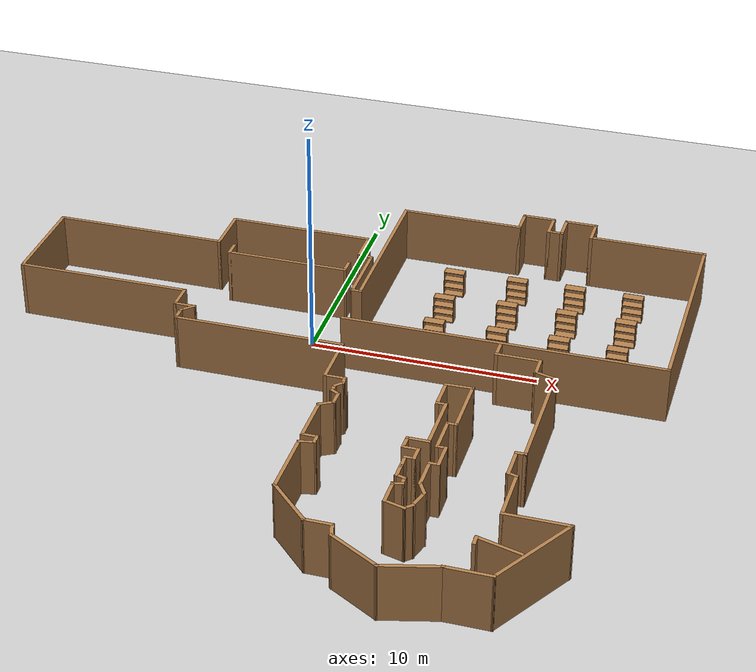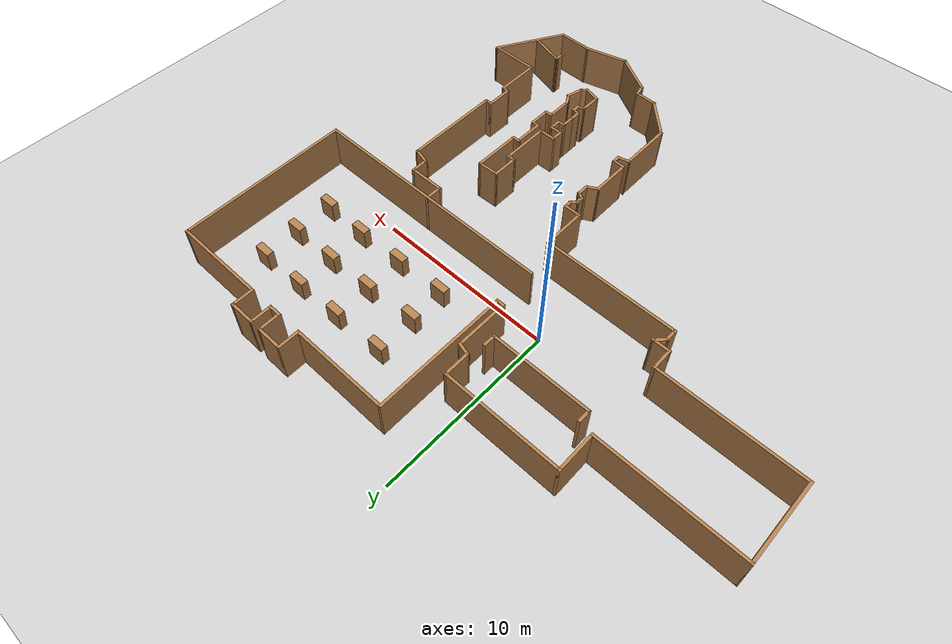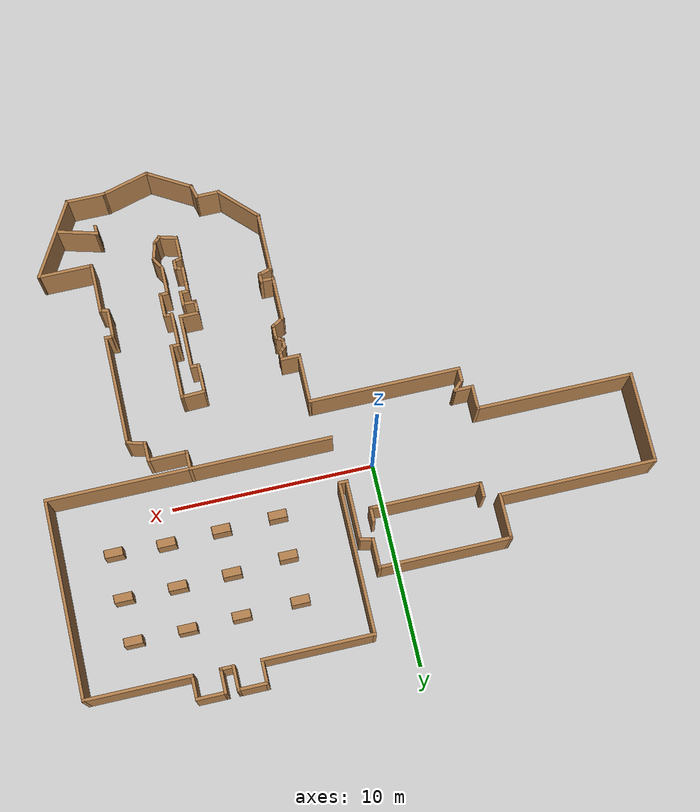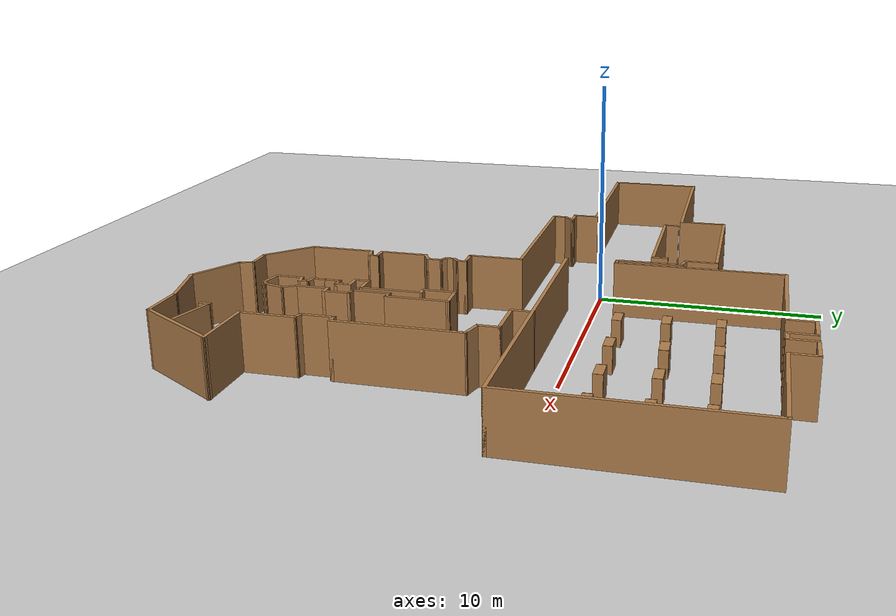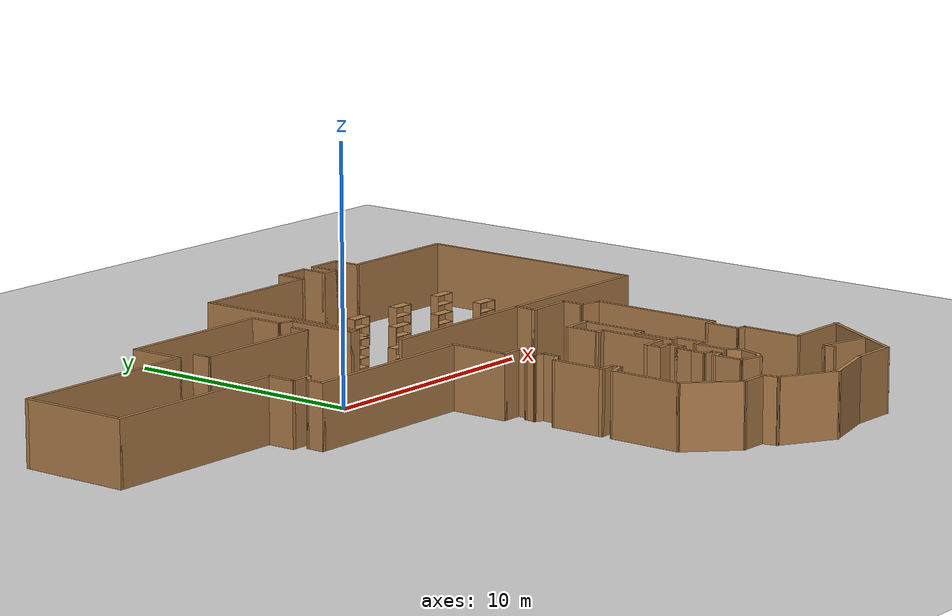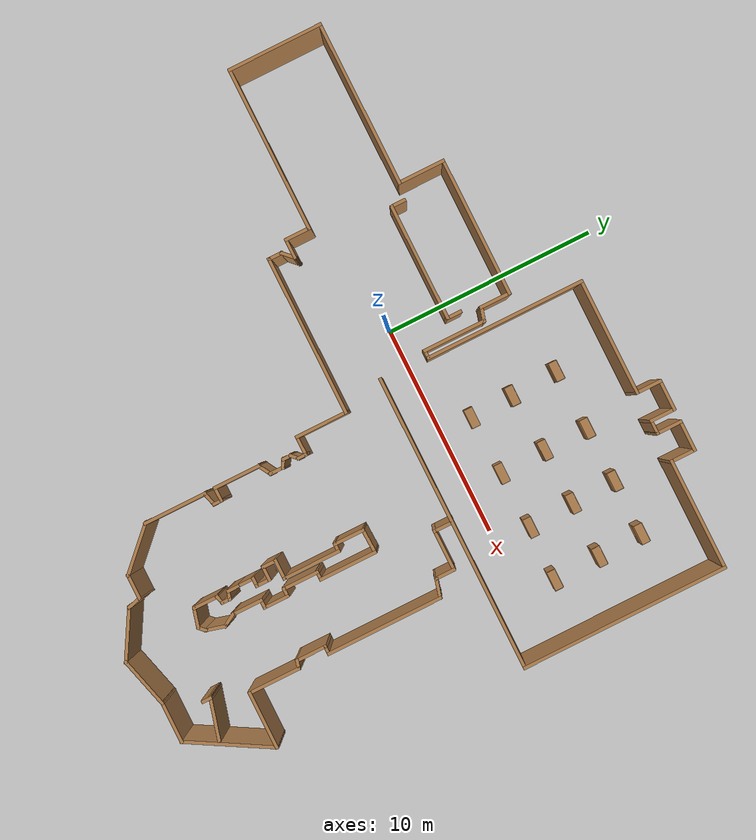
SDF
<sdf version="1.6">
 <world name="default">
  <light name="sun" type="directional">
   <pose>0 0 10 0 -0 0</pose>
   <diffuse>0.8 0.8 0.8 1</diffuse>
   <specular>0.1 0.1 0.1 1</specular>
   <attenuation>
    <range>1000</range>
    <constant>0.9</constant>
    <linear>0.01</linear>
    <quadratic>0.001</quadratic>
   </attenuation>
   <direction>-0.5 0.5 -1</direction>
  </light>
  <model name="ground_plane">
   <static>1</static>
   <link name="link">
    <collision name="collision">
     <geometry><plane><normal>0 0 1</normal><size>100 100</size></plane></geometry>
     <surface><friction><ode><mu>100</mu><mu2>50</mu2></ode></friction></surface>
    </collision>
    <visual name="visual">
     <cast_shadows>0</cast_shadows>
     <geometry><plane><normal>0 0 1</normal><size>100 100</size></plane></geometry>
     <material>
      <script><uri>file://media/materials/scripts/gazebo.material</uri><name>Gazebo/Grey</name></script>
     </material>
    </visual>
   </link>
  </model>
  <gravity>0 0 -9.8</gravity>
  <magnetic_field>6e-06 2.3e-05 -4.2e-05</magnetic_field>
  <atmosphere type="adiabatic"/>
  <physics name="default_physics" default="0" type="ode">
   <max_step_size>0.001</max_step_size>
   <real_time_factor>1</real_time_factor>
   <real_time_update_rate>1000</real_time_update_rate>
  </physics>
  <scene><ambient>0.4 0.4 0.4 1</ambient><background>0.7 0.7 0.7 1</background><shadows>1</shadows></scene>
  <spherical_coordinates>
   <surface_model>EARTH_WGS84</surface_model>
   <latitude_deg>0</latitude_deg>
   <longitude_deg>0</longitude_deg>
   <elevation>0</elevation>
   <heading_deg>0</heading_deg>
  </spherical_coordinates>
  <model name="Robita_0">
   <pose>1.32667 -3.55766 0 0 -0 0</pose>
   <link name="Wall_0">
    <collision name="Wall_0_Collision">
     <geometry><box><size>4.5 0.15 2.5</size></box></geometry>
     <pose>0 0 1.25 0 -0 0</pose>
    </collision>
    <visual name="Wall_0_Visual">
     <pose>0 0 1.25 0 -0 0</pose>
     <geometry><box><size>4.5 0.15 2.5</size></box></geometry>
     <material>
      <script><uri>file://media/materials/scripts/gazebo.material</uri><name>Gazebo/Wood</name></script>
      <ambient>1 1 1 1</ambient>
     </material>
    </visual>
    <pose>-14.3148 4.60052 0 0 0 -1.5708</pose>
   </link>
   <link name="Wall_1">
    <collision name="Wall_1_Collision">
     <geometry><box><size>7.75 0.15 2.5</size></box></geometry>
     <pose>0 0 1.25 0 -0 0</pose>
    </collision>
    <visual name="Wall_1_Visual">
     <pose>0 0 1.25 0 -0 0</pose>
     <geometry><box><size>7.75 0.15 2.5</size></box></geometry>
     <material>
      <script><uri>file://media/materials/scripts/gazebo.material</uri><name>Gazebo/Wood</name></script>
      <ambient>1 1 1 1</ambient>
     </material>
    </visual>
    <pose>-10.5148 2.42552 0 0 -0 0</pose>
   </link>
   <link name="Wall_10">
    <collision name="Wall_10_Collision">
     <geometry><box><size>0.5 0.15 2.5</size></box></geometry>
     <pose>0 0 1.25 0 -0 0</pose>
    </collision>
    <visual name="Wall_10_Visual">
     <pose>0 0 1.25 0 -0 0</pose>
     <geometry><box><size>0.5 0.15 2.5</size></box></geometry>
     <material>
      <script><uri>file://media/materials/scripts/gazebo.material</uri><name>Gazebo/Wood</name></script>
      <ambient>1 1 1 1</ambient>
     </material>
    </visual>
    <pose>1.91096 -2.22374 0 0 0 -1.5708</pose>
   </link>
   <link name="Wall_101">
    <collision name="Wall_101_Collision">
     <geometry><box><size>9.75 0.15 2.5</size></box></geometry>
     <pose>0 0 1.25 0 -0 0</pose>
    </collision>
    <visual name="Wall_101_Visual">
     <pose>0 0 1.25 0 -0 0</pose>
     <geometry><box><size>9.75 0.15 2.5</size></box></geometry>
     <material>
      <script><uri>file://media/materials/scripts/gazebo.material</uri><name>Gazebo/Wood</name></script>
      <ambient>1 1 1 1</ambient>
     </material>
    </visual>
    <pose>14.3148 7.07023 0 0 0 -1.5708</pose>
   </link>
   <link name="Wall_104">
    <collision name="Wall_104_Collision">
     <geometry><box><size>14 0.15 2.5</size></box></geometry>
     <pose>0 0 1.25 0 -0 0</pose>
    </collision>
    <visual name="Wall_104_Visual">
     <pose>0 0 1.25 0 -0 0</pose>
     <geometry><box><size>14 0.15 2.5</size></box></geometry>
     <material>
      <script><uri>file://media/materials/scripts/gazebo.material</uri><name>Gazebo/Wood</name></script>
      <ambient>1 1 1 1</ambient>
     </material>
    </visual>
    <pose>7.38978 2.27023 0 0 -0 3.14159</pose>
   </link>
   <link name="Wall_108">
    <collision name="Wall_108_Collision">
     <geometry><box><size>1 0.15 2.5</size></box></geometry>
     <pose>0 0 1.25 0 -0 0</pose>
    </collision>
    <visual name="Wall_108_Visual">
     <pose>0 0 1.25 0 -0 0</pose>
     <geometry><box><size>1 0.15 2.5</size></box></geometry>
     <material>
      <script><uri>file://media/materials/scripts/gazebo.material</uri><name>Gazebo/Wood</name></script>
      <ambient>1 1 1 1</ambient>
     </material>
    </visual>
    <pose>7.33038 1.85173 0 0 -0 1.5708</pose>
   </link>
   <link name="Wall_11">
    <collision name="Wall_11_Collision">
     <geometry><box><size>0.5 0.15 2.5</size></box></geometry>
     <pose>0 0 1.25 0 -0 0</pose>
    </collision>
    <visual name="Wall_11_Visual">
     <pose>0 0 1.25 0 -0 0</pose>
     <geometry><box><size>0.5 0.15 2.5</size></box></geometry>
     <material>
      <script><uri>file://media/materials/scripts/gazebo.material</uri><name>Gazebo/Wood</name></script>
      <ambient>1 1 1 1</ambient>
     </material>
    </visual>
    <pose>1.78721 -2.52249 0 0 0 -2.35619</pose>
   </link>
   <link name="Wall_110">
    <collision name="Wall_110_Collision">
     <geometry><box><size>1.5 0.15 2.5</size></box></geometry>
     <pose>0 0 1.25 0 -0 0</pose>
    </collision>
    <visual name="Wall_110_Visual">
     <pose>0 0 1.25 0 -0 0</pose>
     <geometry><box><size>1.5 0.15 2.5</size></box></geometry>
     <material>
      <script><uri>file://media/materials/scripts/gazebo.material</uri><name>Gazebo/Wood</name></script>
      <ambient>1 1 1 1</ambient>
     </material>
    </visual>
    <pose>5.90773 -1.97726 0 0 0 -1.57103</pose>
   </link>
   <link name="Wall_118">
    <collision name="Wall_118_Collision">
     <geometry><box><size>0.5 0.15 2.5</size></box></geometry>
     <pose>0 0 1.25 0 -0 0</pose>
    </collision>
    <visual name="Wall_118_Visual">
     <pose>0 0 1.25 0 -0 0</pose>
     <geometry><box><size>0.5 0.15 2.5</size></box></geometry>
     <material>
      <script><uri>file://media/materials/scripts/gazebo.material</uri><name>Gazebo/Wood</name></script>
      <ambient>1 1 1 1</ambient>
     </material>
    </visual>
    <pose>6.08258 -2.65212 0 0 -0 0</pose>
   </link>
   <link name="Wall_119">
    <collision name="Wall_119_Collision">
     <geometry><box><size>2.75 0.15 2.5</size></box></geometry>
     <pose>0 0 1.25 0 -0 0</pose>
    </collision>
    <visual name="Wall_119_Visual">
     <pose>0 0 1.25 0 -0 0</pose>
     <geometry><box><size>2.75 0.15 2.5</size></box></geometry>
     <material>
      <script><uri>file://media/materials/scripts/gazebo.material</uri><name>Gazebo/Wood</name></script>
      <ambient>1 1 1 1</ambient>
     </material>
    </visual>
    <pose>6.25773 -3.95226 0 0 0 -1.57068</pose>
   </link>
   <link name="Wall_12">
    <collision name="Wall_12_Collision">
     <geometry><box><size>0.5 0.15 2.5</size></box></geometry>
     <pose>0 0 1.25 0 -0 0</pose>
    </collision>
    <visual name="Wall_12_Visual">
     <pose>0 0 1.25 0 -0 0</pose>
     <geometry><box><size>0.5 0.15 2.5</size></box></geometry>
     <material>
      <script><uri>file://media/materials/scripts/gazebo.material</uri><name>Gazebo/Wood</name></script>
      <ambient>1 1 1 1</ambient>
     </material>
    </visual>
    <pose>1.66347 -2.82123 0 0 0 -1.5708</pose>
   </link>
   <link name="Wall_127">
    <collision name="Wall_127_Collision">
     <geometry><box><size>1 0.15 2.5</size></box></geometry>
     <pose>0 0 1.25 0 -0 0</pose>
    </collision>
    <visual name="Wall_127_Visual">
     <pose>0 0 1.25 0 -0 0</pose>
     <geometry><box><size>1 0.15 2.5</size></box></geometry>
     <material>
      <script><uri>file://media/materials/scripts/gazebo.material</uri><name>Gazebo/Wood</name></script>
      <ambient>1 1 1 1</ambient>
     </material>
    </visual>
    <pose>5.83289 -5.25239 0 0 -0 3.14159</pose>
   </link>
   <link name="Wall_128">
    <collision name="Wall_128_Collision">
     <geometry><box><size>0.75 0.15 2.5</size></box></geometry>
     <pose>0 0 1.25 0 -0 0</pose>
    </collision>
    <visual name="Wall_128_Visual">
     <pose>0 0 1.25 0 -0 0</pose>
     <geometry><box><size>0.75 0.15 2.5</size></box></geometry>
     <material>
      <script><uri>file://media/materials/scripts/gazebo.material</uri><name>Gazebo/Wood</name></script>
      <ambient>1 1 1 1</ambient>
     </material>
    </visual>
    <pose>5.40789 -5.55239 0 0 0 -1.5708</pose>
   </link>
   <link name="Wall_129">
    <collision name="Wall_129_Collision">
     <geometry><box><size>0.75 0.15 2.5</size></box></geometry>
     <pose>0 0 1.25 0 -0 0</pose>
    </collision>
    <visual name="Wall_129_Visual">
     <pose>0 0 1.25 0 -0 0</pose>
     <geometry><box><size>0.75 0.15 2.5</size></box></geometry>
     <material>
      <script><uri>file://media/materials/scripts/gazebo.material</uri><name>Gazebo/Wood</name></script>
      <ambient>1 1 1 1</ambient>
     </material>
    </visual>
    <pose>5.70789 -5.85239 0 0 -0 0</pose>
   </link>
   <link name="Wall_13">
    <collision name="Wall_13_Collision">
     <geometry><box><size>0.5 0.15 2.5</size></box></geometry>
     <pose>0 0 1.25 0 -0 0</pose>
    </collision>
    <visual name="Wall_13_Visual">
     <pose>0 0 1.25 0 -0 0</pose>
     <geometry><box><size>0.5 0.15 2.5</size></box></geometry>
     <material>
      <script><uri>file://media/materials/scripts/gazebo.material</uri><name>Gazebo/Wood</name></script>
      <ambient>1 1 1 1</ambient>
     </material>
    </visual>
    <pose>1.81503 -3.08373 0 0 0 -0.523599</pose>
   </link>
   <link name="Wall_130">
    <collision name="Wall_130_Collision">
     <geometry><box><size>0.75 0.15 2.5</size></box></geometry>
     <pose>0 0 1.25 0 -0 0</pose>
    </collision>
    <visual name="Wall_130_Visual">
     <pose>0 0 1.25 0 -0 0</pose>
     <geometry><box><size>0.75 0.15 2.5</size></box></geometry>
     <material>
      <script><uri>file://media/materials/scripts/gazebo.material</uri><name>Gazebo/Wood</name></script>
      <ambient>1 1 1 1</ambient>
     </material>
    </visual>
    <pose>6.00789 -6.15239 0 0 0 -1.5708</pose>
   </link>
   <link name="Wall_131">
    <collision name="Wall_131_Collision">
     <geometry><box><size>0.5 0.15 2.5</size></box></geometry>
     <pose>0 0 1.25 0 -0 0</pose>
    </collision>
    <visual name="Wall_131_Visual">
     <pose>0 0 1.25 0 -0 0</pose>
     <geometry><box><size>0.5 0.15 2.5</size></box></geometry>
     <material>
      <script><uri>file://media/materials/scripts/gazebo.material</uri><name>Gazebo/Wood</name></script>
      <ambient>1 1 1 1</ambient>
     </material>
    </visual>
    <pose>5.83289 -6.45239 0 0 -0 3.14159</pose>
   </link>
   <link name="Wall_132">
    <collision name="Wall_132_Collision">
     <geometry><box><size>0.75 0.15 2.5</size></box></geometry>
     <pose>0 0 1.25 0 -0 0</pose>
    </collision>
    <visual name="Wall_132_Visual">
     <pose>0 0 1.25 0 -0 0</pose>
     <geometry><box><size>0.75 0.15 2.5</size></box></geometry>
     <material>
      <script><uri>file://media/materials/scripts/gazebo.material</uri><name>Gazebo/Wood</name></script>
      <ambient>1 1 1 1</ambient>
     </material>
    </visual>
    <pose>5.65789 -6.75239 0 0 0 -1.5708</pose>
   </link>
   <link name="Wall_133">
    <collision name="Wall_133_Collision">
     <geometry><box><size>0.75 0.15 2.5</size></box></geometry>
     <pose>0 0 1.25 0 -0 0</pose>
    </collision>
    <visual name="Wall_133_Visual">
     <pose>0 0 1.25 0 -0 0</pose>
     <geometry><box><size>0.75 0.15 2.5</size></box></geometry>
     <material>
      <script><uri>file://media/materials/scripts/gazebo.material</uri><name>Gazebo/Wood</name></script>
      <ambient>1 1 1 1</ambient>
     </material>
    </visual>
    <pose>5.65789 -7.35239 0 0 0 -1.5708</pose>
   </link>
   <link name="Wall_134">
    <collision name="Wall_134_Collision">
     <geometry><box><size>0.5 0.15 2.5</size></box></geometry>
     <pose>0 0 1.25 0 -0 0</pose>
    </collision>
    <visual name="Wall_134_Visual">
     <pose>0 0 1.25 0 -0 0</pose>
     <geometry><box><size>0.5 0.15 2.5</size></box></geometry>
     <material>
      <script><uri>file://media/materials/scripts/gazebo.material</uri><name>Gazebo/Wood</name></script>
      <ambient>1 1 1 1</ambient>
     </material>
    </visual>
    <pose>5.82692 -7.69768 0 0 0 -0.261799</pose>
   </link>
   <link name="Wall_135">
    <collision name="Wall_135_Collision">
     <geometry><box><size>0.5 0.15 2.5</size></box></geometry>
     <pose>0 0 1.25 0 -0 0</pose>
    </collision>
    <visual name="Wall_135_Visual">
     <pose>0 0 1.25 0 -0 0</pose>
     <geometry><box><size>0.5 0.15 2.5</size></box></geometry>
     <material>
      <script><uri>file://media/materials/scripts/gazebo.material</uri><name>Gazebo/Wood</name></script>
      <ambient>1 1 1 1</ambient>
     </material>
    </visual>
    <pose>5.99596 -7.91798 0 0 0 -1.5708</pose>
   </link>
   <link name="Wall_136">
    <collision name="Wall_136_Collision">
     <geometry><box><size>0.5 0.15 2.5</size></box></geometry>
     <pose>0 0 1.25 0 -0 0</pose>
    </collision>
    <visual name="Wall_136_Visual">
     <pose>0 0 1.25 0 -0 0</pose>
     <geometry><box><size>0.5 0.15 2.5</size></box></geometry>
     <material>
      <script><uri>file://media/materials/scripts/gazebo.material</uri><name>Gazebo/Wood</name></script>
      <ambient>1 1 1 1</ambient>
     </material>
    </visual>
    <pose>5.82692 -8.13827 0 0 0 -2.87979</pose>
   </link>
   <link name="Wall_137">
    <collision name="Wall_137_Collision">
     <geometry><box><size>1.25 0.15 2.5</size></box></geometry>
     <pose>0 0 1.25 0 -0 0</pose>
    </collision>
    <visual name="Wall_137_Visual">
     <pose>0 0 1.25 0 -0 0</pose>
     <geometry><box><size>1.25 0.15 2.5</size></box></geometry>
     <material>
      <script><uri>file://media/materials/scripts/gazebo.material</uri><name>Gazebo/Wood</name></script>
      <ambient>1 1 1 1</ambient>
     </material>
    </visual>
    <pose>5.65789 -8.73356 0 0 0 -1.5708</pose>
   </link>
   <link name="Wall_139">
    <collision name="Wall_139_Collision">
     <geometry><box><size>1 0.15 2.5</size></box></geometry>
     <pose>0 0 1.25 0 -0 0</pose>
    </collision>
    <visual name="Wall_139_Visual">
     <pose>0 0 1.25 0 -0 0</pose>
     <geometry><box><size>1 0.15 2.5</size></box></geometry>
     <material>
      <script><uri>file://media/materials/scripts/gazebo.material</uri><name>Gazebo/Wood</name></script>
      <ambient>1 1 1 1</ambient>
     </material>
    </visual>
    <pose>6.06841 -9.39356 0 0 0 -0.261799</pose>
   </link>
   <link name="Wall_14">
    <collision name="Wall_14_Collision">
     <geometry><box><size>0.75 0.15 2.5</size></box></geometry>
     <pose>0 0 1.25 0 -0 0</pose>
    </collision>
    <visual name="Wall_14_Visual">
     <pose>0 0 1.25 0 -0 0</pose>
     <geometry><box><size>0.75 0.15 2.5</size></box></geometry>
     <material>
      <script><uri>file://media/materials/scripts/gazebo.material</uri><name>Gazebo/Wood</name></script>
      <ambient>1 1 1 1</ambient>
     </material>
    </visual>
    <pose>1.96658 -3.47123 0 0 0 -1.5708</pose>
   </link>
   <link name="Wall_140">
    <collision name="Wall_140_Collision">
     <geometry><box><size>0.5 0.15 2.5</size></box></geometry>
     <pose>0 0 1.25 0 -0 0</pose>
    </collision>
    <visual name="Wall_140_Visual">
     <pose>0 0 1.25 0 -0 0</pose>
     <geometry><box><size>0.5 0.15 2.5</size></box></geometry>
     <material>
      <script><uri>file://media/materials/scripts/gazebo.material</uri><name>Gazebo/Wood</name></script>
      <ambient>1 1 1 1</ambient>
     </material>
    </visual>
    <pose>6.60267 -9.37982 0 0 -0 0.785398</pose>
   </link>
   <link name="Wall_141">
    <collision name="Wall_141_Collision">
     <geometry><box><size>1 0.15 2.5</size></box></geometry>
     <pose>0 0 1.25 0 -0 0</pose>
    </collision>
    <visual name="Wall_141_Visual">
     <pose>0 0 1.25 0 -0 0</pose>
     <geometry><box><size>1 0.15 2.5</size></box></geometry>
     <material>
      <script><uri>file://media/materials/scripts/gazebo.material</uri><name>Gazebo/Wood</name></script>
      <ambient>1 1 1 1</ambient>
     </material>
    </visual>
    <pose>6.83641 -8.84555 0 0 -0 1.309</pose>
   </link>
   <link name="Wall_142">
    <collision name="Wall_142_Collision">
     <geometry><box><size>0.75 0.15 2.5</size></box></geometry>
     <pose>0 0 1.25 0 -0 0</pose>
    </collision>
    <visual name="Wall_142_Visual">
     <pose>0 0 1.25 0 -0 0</pose>
     <geometry><box><size>0.75 0.15 2.5</size></box></geometry>
     <material>
      <script><uri>file://media/materials/scripts/gazebo.material</uri><name>Gazebo/Wood</name></script>
      <ambient>1 1 1 1</ambient>
     </material>
    </visual>
    <pose>6.79641 -8.17523 0 0 -0 2.0944</pose>
   </link>
   <link name="Wall_143">
    <collision name="Wall_143_Collision">
     <geometry><box><size>1.5 0.15 2.5</size></box></geometry>
     <pose>0 0 1.25 0 -0 0</pose>
    </collision>
    <visual name="Wall_143_Visual">
     <pose>0 0 1.25 0 -0 0</pose>
     <geometry><box><size>1.5 0.15 2.5</size></box></geometry>
     <material>
      <script><uri>file://media/materials/scripts/gazebo.material</uri><name>Gazebo/Wood</name></script>
      <ambient>1 1 1 1</ambient>
     </material>
    </visual>
    <pose>6.64641 -7.24042 0 0 -0 1.5708</pose>
   </link>
   <link name="Wall_148">
    <collision name="Wall_148_Collision">
     <geometry><box><size>0.5 0.15 2.5</size></box></geometry>
     <pose>0 0 1.25 0 -0 0</pose>
    </collision>
    <visual name="Wall_148_Visual">
     <pose>0 0 1.25 0 -0 0</pose>
     <geometry><box><size>0.5 0.15 2.5</size></box></geometry>
     <material>
      <script><uri>file://media/materials/scripts/gazebo.material</uri><name>Gazebo/Wood</name></script>
      <ambient>1 1 1 1</ambient>
     </material>
    </visual>
    <pose>6.82141 -6.56542 0 0 -0 0</pose>
   </link>
   <link name="Wall_149">
    <collision name="Wall_149_Collision">
     <geometry><box><size>1.25 0.15 2.5</size></box></geometry>
     <pose>0 0 1.25 0 -0 0</pose>
    </collision>
    <visual name="Wall_149_Visual">
     <pose>0 0 1.25 0 -0 0</pose>
     <geometry><box><size>1.25 0.15 2.5</size></box></geometry>
     <material>
      <script><uri>file://media/materials/scripts/gazebo.material</uri><name>Gazebo/Wood</name></script>
      <ambient>1 1 1 1</ambient>
     </material>
    </visual>
    <pose>6.99649 -6.01527 0 0 -0 1.57064</pose>
   </link>
   <link name="Wall_15">
    <collision name="Wall_15_Collision">
     <geometry><box><size>0.75 0.15 2.5</size></box></geometry>
     <pose>0 0 1.25 0 -0 0</pose>
    </collision>
    <visual name="Wall_15_Visual">
     <pose>0 0 1.25 0 -0 0</pose>
     <geometry><box><size>0.75 0.15 2.5</size></box></geometry>
     <material>
      <script><uri>file://media/materials/scripts/gazebo.material</uri><name>Gazebo/Wood</name></script>
      <ambient>1 1 1 1</ambient>
     </material>
    </visual>
    <pose>1.70677 -3.92123 0 0 0 -2.61799</pose>
   </link>
   <link name="Wall_154">
    <collision name="Wall_154_Collision">
     <geometry><box><size>0.5 0.15 2.5</size></box></geometry>
     <pose>0 0 1.25 0 -0 0</pose>
    </collision>
    <visual name="Wall_154_Visual">
     <pose>0 0 1.25 0 -0 0</pose>
     <geometry><box><size>0.5 0.15 2.5</size></box></geometry>
     <material>
      <script><uri>file://media/materials/scripts/gazebo.material</uri><name>Gazebo/Wood</name></script>
      <ambient>1 1 1 1</ambient>
     </material>
    </visual>
    <pose>6.82158 -5.46512 0 0 -0 3.14159</pose>
   </link>
   <link name="Wall_155">
    <collision name="Wall_155_Collision">
     <geometry><box><size>1.75 0.15 2.5</size></box></geometry>
     <pose>0 0 1.25 0 -0 0</pose>
    </collision>
    <visual name="Wall_155_Visual">
     <pose>0 0 1.25 0 -0 0</pose>
     <geometry><box><size>1.75 0.15 2.5</size></box></geometry>
     <material>
      <script><uri>file://media/materials/scripts/gazebo.material</uri><name>Gazebo/Wood</name></script>
      <ambient>1 1 1 1</ambient>
     </material>
    </visual>
    <pose>6.64649 -4.66527 0 0 -0 1.5709</pose>
   </link>
   <link name="Wall_156">
    <collision name="Wall_156_Collision">
     <geometry><box><size>0.5 0.15 2.5</size></box></geometry>
     <pose>0 0 1.25 0 -0 0</pose>
    </collision>
    <visual name="Wall_156_Visual">
     <pose>0 0 1.25 0 -0 0</pose>
     <geometry><box><size>0.5 0.15 2.5</size></box></geometry>
     <material>
      <script><uri>file://media/materials/scripts/gazebo.material</uri><name>Gazebo/Wood</name></script>
      <ambient>1 1 1 1</ambient>
     </material>
    </visual>
    <pose>6.82141 -3.86542 0 0 -0 0</pose>
   </link>
   <link name="Wall_16">
    <collision name="Wall_16_Collision">
     <geometry><box><size>2.25 0.15 2.5</size></box></geometry>
     <pose>0 0 1.25 0 -0 0</pose>
    </collision>
    <visual name="Wall_16_Visual">
     <pose>0 0 1.25 0 -0 0</pose>
     <geometry><box><size>2.25 0.15 2.5</size></box></geometry>
     <material>
      <script><uri>file://media/materials/scripts/gazebo.material</uri><name>Gazebo/Wood</name></script>
      <ambient>1 1 1 1</ambient>
     </material>
    </visual>
    <pose>1.44697 -5.12123 0 0 0 -1.5708</pose>
   </link>
   <link name="Wall_161">
    <collision name="Wall_161_Collision">
     <geometry><box><size>2.75 0.15 2.5</size></box></geometry>
     <pose>0 0 1.25 0 -0 0</pose>
    </collision>
    <visual name="Wall_161_Visual">
     <pose>0 0 1.25 0 -0 0</pose>
     <geometry><box><size>2.75 0.15 2.5</size></box></geometry>
     <material>
      <script><uri>file://media/materials/scripts/gazebo.material</uri><name>Gazebo/Wood</name></script>
      <ambient>1 1 1 1</ambient>
     </material>
    </visual>
    <pose>6.99641 -2.56542 0 0 -0 1.5708</pose>
   </link>
   <link name="Wall_162">
    <collision name="Wall_162_Collision">
     <geometry><box><size>1.23915 0.15 2.5</size></box></geometry>
     <pose>0 0 1.25 0 -0 0</pose>
    </collision>
    <visual name="Wall_162_Visual">
     <pose>0 0 1.25 0 -0 0</pose>
     <geometry><box><size>1.23915 0.15 2.5</size></box></geometry>
     <material>
      <script><uri>file://media/materials/scripts/gazebo.material</uri><name>Gazebo/Wood</name></script>
      <ambient>1 1 1 1</ambient>
     </material>
    </visual>
    <pose>6.45215 -1.28391 0 0 0 -3.10764</pose>
   </link>
   <link name="Wall_164">
    <collision name="Wall_164_Collision">
     <geometry><box><size>0.5 0.15 2.5</size></box></geometry>
     <pose>0 0 1.25 0 -0 0</pose>
    </collision>
    <visual name="Wall_164_Visual">
     <pose>0 0 1.25 0 -0 0</pose>
     <geometry><box><size>0.5 0.15 2.5</size></box></geometry>
     <material>
      <script><uri>file://media/materials/scripts/gazebo.material</uri><name>Gazebo/Wood</name></script>
      <ambient>1 1 1 1</ambient>
     </material>
    </visual>
    <pose>9.42037 -10.5646 0 0 -0 1.5708</pose>
   </link>
   <link name="Wall_165">
    <collision name="Wall_165_Collision">
     <geometry><box><size>2 0.15 2.5</size></box></geometry>
     <pose>0 0 1.25 0 -0 0</pose>
    </collision>
    <visual name="Wall_165_Visual">
     <pose>0 0 1.25 0 -0 0</pose>
     <geometry><box><size>2 0.15 2.5</size></box></geometry>
     <material>
      <script><uri>file://media/materials/scripts/gazebo.material</uri><name>Gazebo/Wood</name></script>
      <ambient>1 1 1 1</ambient>
     </material>
    </visual>
    <pose>10.3139 -10.6291 0 0 0 -0.261799</pose>
   </link>
   <link name="Wall_167">
    <collision name="Wall_167_Collision">
     <geometry><box><size>0.75 0.15 2.5</size></box></geometry>
     <pose>0 0 1.25 0 -0 0</pose>
    </collision>
    <visual name="Wall_167_Visual">
     <pose>0 0 1.25 0 -0 0</pose>
     <geometry><box><size>0.75 0.15 2.5</size></box></geometry>
     <material>
      <script><uri>file://media/materials/scripts/gazebo.material</uri><name>Gazebo/Wood</name></script>
      <ambient>1 1 1 1</ambient>
     </material>
    </visual>
    <pose>-5.94942 6.32688 0 0 0 -1.5708</pose>
   </link>
   <link name="Wall_168">
    <collision name="Wall_168_Collision">
     <geometry><box><size>5.5 0.15 2.5</size></box></geometry>
     <pose>0 0 1.25 0 -0 0</pose>
    </collision>
    <visual name="Wall_168_Visual">
     <pose>0 0 1.25 0 -0 0</pose>
     <geometry><box><size>5.5 0.15 2.5</size></box></geometry>
     <material>
      <script><uri>file://media/materials/scripts/gazebo.material</uri><name>Gazebo/Wood</name></script>
      <ambient>1 1 1 1</ambient>
     </material>
    </visual>
    <pose>-3.27438 6.02704 0 0 -0 6.1e-05</pose>
   </link>
   <link name="Wall_169">
    <collision name="Wall_169_Collision">
     <geometry><box><size>0.75 0.15 2.5</size></box></geometry>
     <pose>0 0 1.25 0 -0 0</pose>
    </collision>
    <visual name="Wall_169_Visual">
     <pose>0 0 1.25 0 -0 0</pose>
     <geometry><box><size>0.75 0.15 2.5</size></box></geometry>
     <material>
      <script><uri>file://media/materials/scripts/gazebo.material</uri><name>Gazebo/Wood</name></script>
      <ambient>1 1 1 1</ambient>
     </material>
    </visual>
    <pose>-0.59934 6.3272 0 0 -0 1.5708</pose>
   </link>
   <link name="Wall_2">
    <collision name="Wall_2_Collision">
     <geometry><box><size>1.25 0.15 2.5</size></box></geometry>
     <pose>0 0 1.25 0 -0 0</pose>
    </collision>
    <visual name="Wall_2_Visual">
     <pose>0 0 1.25 0 -0 0</pose>
     <geometry><box><size>1.25 0.15 2.5</size></box></geometry>
     <material>
      <script><uri>file://media/materials/scripts/gazebo.material</uri><name>Gazebo/Wood</name></script>
      <ambient>1 1 1 1</ambient>
     </material>
    </visual>
    <pose>-6.71478 1.87552 0 0 0 -1.5708</pose>
   </link>
   <link name="Wall_21">
    <collision name="Wall_21_Collision">
     <geometry><box><size>0.75 0.15 2.5</size></box></geometry>
     <pose>0 0 1.25 0 -0 0</pose>
    </collision>
    <visual name="Wall_21_Visual">
     <pose>0 0 1.25 0 -0 0</pose>
     <geometry><box><size>0.75 0.15 2.5</size></box></geometry>
     <material>
      <script><uri>file://media/materials/scripts/gazebo.material</uri><name>Gazebo/Wood</name></script>
      <ambient>1 1 1 1</ambient>
     </material>
    </visual>
    <pose>1.74696 -6.17123 0 0 -0 0</pose>
   </link>
   <link name="Wall_22">
    <collision name="Wall_22_Collision">
     <geometry><box><size>0.5 0.15 2.5</size></box></geometry>
     <pose>0 0 1.25 0 -0 0</pose>
    </collision>
    <visual name="Wall_22_Visual">
     <pose>0 0 1.25 0 -0 0</pose>
     <geometry><box><size>0.5 0.15 2.5</size></box></geometry>
     <material>
      <script><uri>file://media/materials/scripts/gazebo.material</uri><name>Gazebo/Wood</name></script>
      <ambient>1 1 1 1</ambient>
     </material>
    </visual>
    <pose>2.04697 -6.34623 0 0 0 -1.5708</pose>
   </link>
   <link name="Wall_25">
    <collision name="Wall_25_Collision">
     <geometry><box><size>0.75 0.15 2.5</size></box></geometry>
     <pose>0 0 1.25 0 -0 0</pose>
    </collision>
    <visual name="Wall_25_Visual">
     <pose>0 0 1.25 0 -0 0</pose>
     <geometry><box><size>0.75 0.15 2.5</size></box></geometry>
     <material>
      <script><uri>file://media/materials/scripts/gazebo.material</uri><name>Gazebo/Wood</name></script>
      <ambient>1 1 1 1</ambient>
     </material>
    </visual>
    <pose>1.75719 -6.59888 0 0 0 -2.87979</pose>
   </link>
   <link name="Wall_26">
    <collision name="Wall_26_Collision">
     <geometry><box><size>3 0.15 2.5</size></box></geometry>
     <pose>0 0 1.25 0 -0 0</pose>
    </collision>
    <visual name="Wall_26_Visual">
     <pose>0 0 1.25 0 -0 0</pose>
     <geometry><box><size>3 0.15 2.5</size></box></geometry>
     <material>
      <script><uri>file://media/materials/scripts/gazebo.material</uri><name>Gazebo/Wood</name></script>
      <ambient>1 1 1 1</ambient>
     </material>
    </visual>
    <pose>1.46741 -8.10152 0 0 0 -1.5708</pose>
   </link>
   <link name="Wall_27">
    <collision name="Wall_27_Collision">
     <geometry><box><size>2.5 0.15 2.5</size></box></geometry>
     <pose>0 0 1.25 0 -0 0</pose>
    </collision>
    <visual name="Wall_27_Visual">
     <pose>0 0 1.25 0 -0 0</pose>
     <geometry><box><size>2.5 0.15 2.5</size></box></geometry>
     <material>
      <script><uri>file://media/materials/scripts/gazebo.material</uri><name>Gazebo/Wood</name></script>
      <ambient>1 1 1 1</ambient>
     </material>
    </visual>
    <pose>2.29826 -10.3574 0 0 0 -0.785398</pose>
   </link>
   <link name="Wall_29">
    <collision name="Wall_29_Collision">
     <geometry><box><size>1.25 0.15 2.5</size></box></geometry>
     <pose>0 0 1.25 0 -0 0</pose>
    </collision>
    <visual name="Wall_29_Visual">
     <pose>0 0 1.25 0 -0 0</pose>
     <geometry><box><size>1.25 0.15 2.5</size></box></geometry>
     <material>
      <script><uri>file://media/materials/scripts/gazebo.material</uri><name>Gazebo/Wood</name></script>
      <ambient>1 1 1 1</ambient>
     </material>
    </visual>
    <pose>3.67911 -11.1882 0 0 -0 0</pose>
   </link>
   <link name="Wall_3">
    <collision name="Wall_3_Collision">
     <geometry><box><size>1 0.15 2.5</size></box></geometry>
     <pose>0 0 1.25 0 -0 0</pose>
    </collision>
    <visual name="Wall_3_Visual">
     <pose>0 0 1.25 0 -0 0</pose>
     <geometry><box><size>1 0.15 2.5</size></box></geometry>
     <material>
      <script><uri>file://media/materials/scripts/gazebo.material</uri><name>Gazebo/Wood</name></script>
      <ambient>1 1 1 1</ambient>
     </material>
    </visual>
    <pose>-6.28978 1.32552 0 0 -0 0</pose>
   </link>
   <link name="Wall_30">
    <collision name="Wall_30_Collision">
     <geometry><box><size>0.75 0.15 2.5</size></box></geometry>
     <pose>0 0 1.25 0 -0 0</pose>
    </collision>
    <visual name="Wall_30_Visual">
     <pose>0 0 1.25 0 -0 0</pose>
     <geometry><box><size>0.75 0.15 2.5</size></box></geometry>
     <material>
      <script><uri>file://media/materials/scripts/gazebo.material</uri><name>Gazebo/Wood</name></script>
      <ambient>1 1 1 1</ambient>
     </material>
    </visual>
    <pose>4.30676 -11.478 0 0 0 -1.309</pose>
   </link>
   <link name="Wall_31">
    <collision name="Wall_31_Collision">
     <geometry><box><size>2.5 0.15 2.5</size></box></geometry>
     <pose>0 0 1.25 0 -0 0</pose>
    </collision>
    <visual name="Wall_31_Visual">
     <pose>0 0 1.25 0 -0 0</pose>
     <geometry><box><size>2.5 0.15 2.5</size></box></geometry>
     <material>
      <script><uri>file://media/materials/scripts/gazebo.material</uri><name>Gazebo/Wood</name></script>
      <ambient>1 1 1 1</ambient>
     </material>
    </visual>
    <pose>5.40198 -12.3553 0 0 0 -0.523599</pose>
   </link>
   <link name="Wall_34">
    <collision name="Wall_34_Collision">
     <geometry><box><size>2.5 0.15 2.5</size></box></geometry>
     <pose>0 0 1.25 0 -0 0</pose>
    </collision>
    <visual name="Wall_34_Visual">
     <pose>0 0 1.25 0 -0 0</pose>
     <geometry><box><size>2.5 0.15 2.5</size></box></geometry>
     <material>
      <script><uri>file://media/materials/scripts/gazebo.material</uri><name>Gazebo/Wood</name></script>
      <ambient>1 1 1 1</ambient>
     </material>
    </visual>
    <pose>7.55452 -12.6387 0 0 -0 0.261799</pose>
   </link>
   <link name="Wall_35">
    <collision name="Wall_35_Collision">
     <geometry><box><size>2 0.15 2.5</size></box></geometry>
     <pose>0 0 1.25 0 -0 0</pose>
    </collision>
    <visual name="Wall_35_Visual">
     <pose>0 0 1.25 0 -0 0</pose>
     <geometry><box><size>2 0.15 2.5</size></box></geometry>
     <material>
      <script><uri>file://media/materials/scripts/gazebo.material</uri><name>Gazebo/Wood</name></script>
      <ambient>1 1 1 1</ambient>
     </material>
    </visual>
    <pose>9.61449 -12.3346 0 0 -0 0</pose>
   </link>
   <link name="Wall_36">
    <collision name="Wall_36_Collision">
     <geometry><box><size>4.25 0.15 2.5</size></box></geometry>
     <pose>0 0 1.25 0 -0 0</pose>
    </collision>
    <visual name="Wall_36_Visual">
     <pose>0 0 1.25 0 -0 0</pose>
     <geometry><box><size>4.25 0.15 2.5</size></box></geometry>
     <material>
      <script><uri>file://media/materials/scripts/gazebo.material</uri><name>Gazebo/Wood</name></script>
      <ambient>1 1 1 1</ambient>
     </material>
    </visual>
    <pose>11.5645 -10.5592 0 0 -0 1.0472</pose>
   </link>
   <link name="Wall_4">
    <collision name="Wall_4_Collision">
     <geometry><box><size>0.75 0.15 2.5</size></box></geometry>
     <pose>0 0 1.25 0 -0 0</pose>
    </collision>
    <visual name="Wall_4_Visual">
     <pose>0 0 1.25 0 -0 0</pose>
     <geometry><box><size>0.75 0.15 2.5</size></box></geometry>
     <material>
      <script><uri>file://media/materials/scripts/gazebo.material</uri><name>Gazebo/Wood</name></script>
      <ambient>1 1 1 1</ambient>
     </material>
    </visual>
    <pose>-6.0771 1.1132 0 0 0 -2.3562</pose>
   </link>
   <link name="Wall_40">
    <collision name="Wall_40_Collision">
     <geometry><box><size>2.75 0.15 2.5</size></box></geometry>
     <pose>0 0 1.25 0 -0 0</pose>
    </collision>
    <visual name="Wall_40_Visual">
     <pose>0 0 1.25 0 -0 0</pose>
     <geometry><box><size>2.75 0.15 2.5</size></box></geometry>
     <material>
      <script><uri>file://media/materials/scripts/gazebo.material</uri><name>Gazebo/Wood</name></script>
      <ambient>1 1 1 1</ambient>
     </material>
    </visual>
    <pose>11.2895 -8.78385 0 0 -0 3.14159</pose>
   </link>
   <link name="Wall_41">
    <collision name="Wall_41_Collision">
     <geometry><box><size>2.5 0.15 2.5</size></box></geometry>
     <pose>0 0 1.25 0 -0 0</pose>
    </collision>
    <visual name="Wall_41_Visual">
     <pose>0 0 1.25 0 -0 0</pose>
     <geometry><box><size>2.5 0.15 2.5</size></box></geometry>
     <material>
      <script><uri>file://media/materials/scripts/gazebo.material</uri><name>Gazebo/Wood</name></script>
      <ambient>1 1 1 1</ambient>
     </material>
    </visual>
    <pose>9.98949 -7.60885 0 0 -0 1.5708</pose>
   </link>
   <link name="Wall_42">
    <collision name="Wall_42_Collision">
     <geometry><box><size>0.5 0.15 2.5</size></box></geometry>
     <pose>0 0 1.25 0 -0 0</pose>
    </collision>
    <visual name="Wall_42_Visual">
     <pose>0 0 1.25 0 -0 0</pose>
     <geometry><box><size>0.5 0.15 2.5</size></box></geometry>
     <material>
      <script><uri>file://media/materials/scripts/gazebo.material</uri><name>Gazebo/Wood</name></script>
      <ambient>1 1 1 1</ambient>
     </material>
    </visual>
    <pose>9.82045 -6.38856 0 0 -0 2.87979</pose>
   </link>
   <link name="Wall_43">
    <collision name="Wall_43_Collision">
     <geometry><box><size>1.5 0.15 2.5</size></box></geometry>
     <pose>0 0 1.25 0 -0 0</pose>
    </collision>
    <visual name="Wall_43_Visual">
     <pose>0 0 1.25 0 -0 0</pose>
     <geometry><box><size>1.5 0.15 2.5</size></box></geometry>
     <material>
      <script><uri>file://media/materials/scripts/gazebo.material</uri><name>Gazebo/Wood</name></script>
      <ambient>1 1 1 1</ambient>
     </material>
    </visual>
    <pose>9.65141 -5.66826 0 0 -0 1.5708</pose>
   </link>
   <link name="Wall_44">
    <collision name="Wall_44_Collision">
     <geometry><box><size>0.5 0.15 2.5</size></box></geometry>
     <pose>0 0 1.25 0 -0 0</pose>
    </collision>
    <visual name="Wall_44_Visual">
     <pose>0 0 1.25 0 -0 0</pose>
     <geometry><box><size>0.5 0.15 2.5</size></box></geometry>
     <material>
      <script><uri>file://media/materials/scripts/gazebo.material</uri><name>Gazebo/Wood</name></script>
      <ambient>1 1 1 1</ambient>
     </material>
    </visual>
    <pose>9.82641 -4.99326 0 0 -0 0</pose>
   </link>
   <link name="Wall_45">
    <collision name="Wall_45_Collision">
     <geometry><box><size>5.5 0.15 2.5</size></box></geometry>
     <pose>0 0 1.25 0 -0 0</pose>
    </collision>
    <visual name="Wall_45_Visual">
     <pose>0 0 1.25 0 -0 0</pose>
     <geometry><box><size>5.5 0.15 2.5</size></box></geometry>
     <material>
      <script><uri>file://media/materials/scripts/gazebo.material</uri><name>Gazebo/Wood</name></script>
      <ambient>1 1 1 1</ambient>
     </material>
    </visual>
    <pose>10.0014 -2.31826 0 0 -0 1.5708</pose>
   </link>
   <link name="Wall_46">
    <collision name="Wall_46_Collision">
     <geometry><box><size>1 0.15 2.5</size></box></geometry>
     <pose>0 0 1.25 0 -0 0</pose>
    </collision>
    <visual name="Wall_46_Visual">
     <pose>0 0 1.25 0 -0 0</pose>
     <geometry><box><size>1 0.15 2.5</size></box></geometry>
     <material>
      <script><uri>file://media/materials/scripts/gazebo.material</uri><name>Gazebo/Wood</name></script>
      <ambient>1 1 1 1</ambient>
     </material>
    </visual>
    <pose>9.59089 0.466736 0 0 -0 2.87979</pose>
   </link>
   <link name="Wall_47">
    <collision name="Wall_47_Collision">
     <geometry><box><size>1 0.15 2.5</size></box></geometry>
     <pose>0 0 1.25 0 -0 0</pose>
    </collision>
    <visual name="Wall_47_Visual">
     <pose>0 0 1.25 0 -0 0</pose>
     <geometry><box><size>1 0.15 2.5</size></box></geometry>
     <material>
      <script><uri>file://media/materials/scripts/gazebo.material</uri><name>Gazebo/Wood</name></script>
      <ambient>1 1 1 1</ambient>
     </material>
    </visual>
    <pose>9.18038 1.00173 0 0 -0 1.5708</pose>
   </link>
   <link name="Wall_5">
    <collision name="Wall_5_Collision">
     <geometry><box><size>0.75 0.15 2.5</size></box></geometry>
     <pose>0 0 1.25 0 -0 0</pose>
    </collision>
    <visual name="Wall_5_Visual">
     <pose>0 0 1.25 0 -0 0</pose>
     <geometry><box><size>0.75 0.15 2.5</size></box></geometry>
     <material>
      <script><uri>file://media/materials/scripts/gazebo.material</uri><name>Gazebo/Wood</name></script>
      <ambient>1 1 1 1</ambient>
     </material>
    </visual>
    <pose>-6.28942 0.600877 0 0 0 -1.5708</pose>
   </link>
   <link name="Wall_54">
    <collision name="Wall_54_Collision">
     <geometry><box><size>2 0.15 2.5</size></box></geometry>
     <pose>0 0 1.25 0 -0 0</pose>
    </collision>
    <visual name="Wall_54_Visual">
     <pose>0 0 1.25 0 -0 0</pose>
     <geometry><box><size>2 0.15 2.5</size></box></geometry>
     <material>
      <script><uri>file://media/materials/scripts/gazebo.material</uri><name>Gazebo/Wood</name></script>
      <ambient>1 1 1 1</ambient>
     </material>
    </visual>
    <pose>8.25538 1.42673 0 0 -0 3.14159</pose>
   </link>
   <link name="Wall_6">
    <collision name="Wall_6_Collision">
     <geometry><box><size>7.5 0.15 2.5</size></box></geometry>
     <pose>0 0 1.25 0 -0 0</pose>
    </collision>
    <visual name="Wall_6_Visual">
     <pose>0 0 1.25 0 -0 0</pose>
     <geometry><box><size>7.5 0.15 2.5</size></box></geometry>
     <material>
      <script><uri>file://media/materials/scripts/gazebo.material</uri><name>Gazebo/Wood</name></script>
      <ambient>1 1 1 1</ambient>
     </material>
    </visual>
    <pose>-2.61423 0.301067 0 0 -0 5.2e-05</pose>
   </link>
   <link name="Wall_7">
    <collision name="Wall_7_Collision">
     <geometry><box><size>2.5 0.15 2.5</size></box></geometry>
     <pose>0 0 1.25 0 -0 0</pose>
    </collision>
    <visual name="Wall_7_Visual">
     <pose>0 0 1.25 0 -0 0</pose>
     <geometry><box><size>2.5 0.15 2.5</size></box></geometry>
     <material>
      <script><uri>file://media/materials/scripts/gazebo.material</uri><name>Gazebo/Wood</name></script>
      <ambient>1 1 1 1</ambient>
     </material>
    </visual>
    <pose>1.06096 -0.873743 0 0 0 -1.5708</pose>
   </link>
   <link name="Wall_71">
    <collision name="Wall_71_Collision">
     <geometry><box><size>7.75 0.15 2.5</size></box></geometry>
     <pose>0 0 1.25 0 -0 0</pose>
    </collision>
    <visual name="Wall_71_Visual">
     <pose>0 0 1.25 0 -0 0</pose>
     <geometry><box><size>7.75 0.15 2.5</size></box></geometry>
     <material>
      <script><uri>file://media/materials/scripts/gazebo.material</uri><name>Gazebo/Wood</name></script>
      <ambient>1 1 1 1</ambient>
     </material>
    </visual>
    <pose>-10.5148 6.77552 0 0 -0 0</pose>
   </link>
   <link name="Wall_72">
    <collision name="Wall_72_Collision">
     <geometry><box><size>2.25 0.15 2.5</size></box></geometry>
     <pose>0 0 1.25 0 -0 0</pose>
    </collision>
    <visual name="Wall_72_Visual">
     <pose>0 0 1.25 0 -0 0</pose>
     <geometry><box><size>2.25 0.15 2.5</size></box></geometry>
     <material>
      <script><uri>file://media/materials/scripts/gazebo.material</uri><name>Gazebo/Wood</name></script>
      <ambient>1 1 1 1</ambient>
     </material>
    </visual>
    <pose>-6.71478 7.82552 0 0 -0 1.5708</pose>
   </link>
   <link name="Wall_73">
    <collision name="Wall_73_Collision">
     <geometry><box><size>6.5 0.15 2.5</size></box></geometry>
     <pose>0 0 1.25 0 -0 0</pose>
    </collision>
    <visual name="Wall_73_Visual">
     <pose>0 0 1.25 0 -0 0</pose>
     <geometry><box><size>6.5 0.15 2.5</size></box></geometry>
     <material>
      <script><uri>file://media/materials/scripts/gazebo.material</uri><name>Gazebo/Wood</name></script>
      <ambient>1 1 1 1</ambient>
     </material>
    </visual>
    <pose>-3.53978 8.87552 0 0 -0 0</pose>
   </link>
   <link name="Wall_74">
    <collision name="Wall_74_Collision">
     <geometry><box><size>1.5 0.15 2.5</size></box></geometry>
     <pose>0 0 1.25 0 -0 0</pose>
    </collision>
    <visual name="Wall_74_Visual">
     <pose>0 0 1.25 0 -0 0</pose>
     <geometry><box><size>1.5 0.15 2.5</size></box></geometry>
     <material>
      <script><uri>file://media/materials/scripts/gazebo.material</uri><name>Gazebo/Wood</name></script>
      <ambient>1 1 1 1</ambient>
     </material>
    </visual>
    <pose>-0.364778 8.20052 0 0 0 -1.5708</pose>
   </link>
   <link name="Wall_75">
    <collision name="Wall_75_Collision">
     <geometry><box><size>0.75 0.15 2.5</size></box></geometry>
     <pose>0 0 1.25 0 -0 0</pose>
    </collision>
    <visual name="Wall_75_Visual">
     <pose>0 0 1.25 0 -0 0</pose>
     <geometry><box><size>0.75 0.15 2.5</size></box></geometry>
     <material>
      <script><uri>file://media/materials/scripts/gazebo.material</uri><name>Gazebo/Wood</name></script>
      <ambient>1 1 1 1</ambient>
     </material>
    </visual>
    <pose>-0.075 7.44788 0 0 0 -0.261799</pose>
   </link>
   <link name="Wall_76">
    <collision name="Wall_76_Collision">
     <geometry><box><size>3 0.15 2.5</size></box></geometry>
     <pose>0 0 1.25 0 -0 0</pose>
    </collision>
    <visual name="Wall_76_Visual">
     <pose>0 0 1.25 0 -0 0</pose>
     <geometry><box><size>3 0.15 2.5</size></box></geometry>
     <material>
      <script><uri>file://media/materials/scripts/gazebo.material</uri><name>Gazebo/Wood</name></script>
      <ambient>1 1 1 1</ambient>
     </material>
    </visual>
    <pose>0.214778 5.94523 0 0 0 -1.5708</pose>
   </link>
   <link name="Wall_77">
    <collision name="Wall_77_Collision">
     <geometry><box><size>0.5 0.15 2.5</size></box></geometry>
     <pose>0 0 1.25 0 -0 0</pose>
    </collision>
    <visual name="Wall_77_Visual">
     <pose>0 0 1.25 0 -0 0</pose>
     <geometry><box><size>0.5 0.15 2.5</size></box></geometry>
     <material>
      <script><uri>file://media/materials/scripts/gazebo.material</uri><name>Gazebo/Wood</name></script>
      <ambient>1 1 1 1</ambient>
     </material>
    </visual>
    <pose>0.389778 4.52023 0 0 -0 0</pose>
   </link>
   <link name="Wall_79">
    <collision name="Wall_79_Collision">
     <geometry><box><size>7.5 0.15 2.5</size></box></geometry>
     <pose>0 0 1.25 0 -0 0</pose>
    </collision>
    <visual name="Wall_79_Visual">
     <pose>0 0 1.25 0 -0 0</pose>
     <geometry><box><size>7.5 0.15 2.5</size></box></geometry>
     <material>
      <script><uri>file://media/materials/scripts/gazebo.material</uri><name>Gazebo/Wood</name></script>
      <ambient>1 1 1 1</ambient>
     </material>
    </visual>
    <pose>0.564778 8.19523 0 0 -0 1.5708</pose>
   </link>
   <link name="Wall_80">
    <collision name="Wall_80_Collision">
     <geometry><box><size>5.5 0.15 2.5</size></box></geometry>
     <pose>0 0 1.25 0 -0 0</pose>
    </collision>
    <visual name="Wall_80_Visual">
     <pose>0 0 1.25 0 -0 0</pose>
     <geometry><box><size>5.5 0.15 2.5</size></box></geometry>
     <material>
      <script><uri>file://media/materials/scripts/gazebo.material</uri><name>Gazebo/Wood</name></script>
      <ambient>1 1 1 1</ambient>
     </material>
    </visual>
    <pose>3.23978 11.8702 0 0 -0 0</pose>
   </link>
   <link name="Wall_82">
    <collision name="Wall_82_Collision">
     <geometry><box><size>1.25 0.15 2.5</size></box></geometry>
     <pose>0 0 1.25 0 -0 0</pose>
    </collision>
    <visual name="Wall_82_Visual">
     <pose>0 0 1.25 0 -0 0</pose>
     <geometry><box><size>1.25 0.15 2.5</size></box></geometry>
     <material>
      <script><uri>file://media/materials/scripts/gazebo.material</uri><name>Gazebo/Wood</name></script>
      <ambient>1 1 1 1</ambient>
     </material>
    </visual>
    <pose>5.91478 12.4202 0 0 -0 1.5708</pose>
   </link>
   <link name="Wall_83">
    <collision name="Wall_83_Collision">
     <geometry><box><size>1.5 0.15 2.5</size></box></geometry>
     <pose>0 0 1.25 0 -0 0</pose>
    </collision>
    <visual name="Wall_83_Visual">
     <pose>0 0 1.25 0 -0 0</pose>
     <geometry><box><size>1.5 0.15 2.5</size></box></geometry>
     <material>
      <script><uri>file://media/materials/scripts/gazebo.material</uri><name>Gazebo/Wood</name></script>
      <ambient>1 1 1 1</ambient>
     </material>
    </visual>
    <pose>6.58978 12.9702 0 0 -0 0</pose>
   </link>
   <link name="Wall_84">
    <collision name="Wall_84_Collision">
     <geometry><box><size>1.25 0.15 2.5</size></box></geometry>
     <pose>0 0 1.25 0 -0 0</pose>
    </collision>
    <visual name="Wall_84_Visual">
     <pose>0 0 1.25 0 -0 0</pose>
     <geometry><box><size>1.25 0.15 2.5</size></box></geometry>
     <material>
      <script><uri>file://media/materials/scripts/gazebo.material</uri><name>Gazebo/Wood</name></script>
      <ambient>1 1 1 1</ambient>
     </material>
    </visual>
    <pose>7.26478 12.4202 0 0 0 -1.5708</pose>
   </link>
   <link name="Wall_85">
    <collision name="Wall_85_Collision">
     <geometry><box><size>0.75 0.15 2.5</size></box></geometry>
     <pose>0 0 1.25 0 -0 0</pose>
    </collision>
    <visual name="Wall_85_Visual">
     <pose>0 0 1.25 0 -0 0</pose>
     <geometry><box><size>0.75 0.15 2.5</size></box></geometry>
     <material>
      <script><uri>file://media/materials/scripts/gazebo.material</uri><name>Gazebo/Wood</name></script>
      <ambient>1 1 1 1</ambient>
     </material>
    </visual>
    <pose>7.56478 11.8702 0 0 -0 0</pose>
   </link>
   <link name="Wall_86">
    <collision name="Wall_86_Collision">
     <geometry><box><size>1.25 0.15 2.5</size></box></geometry>
     <pose>0 0 1.25 0 -0 0</pose>
    </collision>
    <visual name="Wall_86_Visual">
     <pose>0 0 1.25 0 -0 0</pose>
     <geometry><box><size>1.25 0.15 2.5</size></box></geometry>
     <material>
      <script><uri>file://media/materials/scripts/gazebo.material</uri><name>Gazebo/Wood</name></script>
      <ambient>1 1 1 1</ambient>
     </material>
    </visual>
    <pose>7.86478 12.4202 0 0 -0 1.5708</pose>
   </link>
   <link name="Wall_87">
    <collision name="Wall_87_Collision">
     <geometry><box><size>1.5 0.15 2.5</size></box></geometry>
     <pose>0 0 1.25 0 -0 0</pose>
    </collision>
    <visual name="Wall_87_Visual">
     <pose>0 0 1.25 0 -0 0</pose>
     <geometry><box><size>1.5 0.15 2.5</size></box></geometry>
     <material>
      <script><uri>file://media/materials/scripts/gazebo.material</uri><name>Gazebo/Wood</name></script>
      <ambient>1 1 1 1</ambient>
     </material>
    </visual>
    <pose>8.53978 12.9702 0 0 -0 0</pose>
   </link>
   <link name="Wall_9">
    <collision name="Wall_9_Collision">
     <geometry><box><size>1 0.15 2.5</size></box></geometry>
     <pose>0 0 1.25 0 -0 0</pose>
    </collision>
    <visual name="Wall_9_Visual">
     <pose>0 0 1.25 0 -0 0</pose>
     <geometry><box><size>1 0.15 2.5</size></box></geometry>
     <material>
      <script><uri>file://media/materials/scripts/gazebo.material</uri><name>Gazebo/Wood</name></script>
      <ambient>1 1 1 1</ambient>
     </material>
    </visual>
    <pose>1.48596 -2.04874 0 0 -0 0</pose>
   </link>
   <link name="Wall_90">
    <collision name="Wall_90_Collision">
     <geometry><box><size>1.25 0.15 2.5</size></box></geometry>
     <pose>0 0 1.25 0 -0 0</pose>
    </collision>
    <visual name="Wall_90_Visual">
     <pose>0 0 1.25 0 -0 0</pose>
     <geometry><box><size>1.25 0.15 2.5</size></box></geometry>
     <material>
      <script><uri>file://media/materials/scripts/gazebo.material</uri><name>Gazebo/Wood</name></script>
      <ambient>1 1 1 1</ambient>
     </material>
    </visual>
    <pose>9.21478 12.4202 0 0 0 -1.5708</pose>
   </link>
   <link name="Wall_91">
    <collision name="Wall_91_Collision">
     <geometry><box><size>5.25 0.15 2.5</size></box></geometry>
     <pose>0 0 1.25 0 -0 0</pose>
    </collision>
    <visual name="Wall_91_Visual">
     <pose>0 0 1.25 0 -0 0</pose>
     <geometry><box><size>5.25 0.15 2.5</size></box></geometry>
     <material>
      <script><uri>file://media/materials/scripts/gazebo.material</uri><name>Gazebo/Wood</name></script>
      <ambient>1 1 1 1</ambient>
     </material>
    </visual>
    <pose>11.7648 11.8702 0 0 -0 0</pose>
   </link>
   <static>1</static>
  </model>
  <model name="bookshelf">
   <static>1</static>
   <link name="link">
    <inertial><mass>1</mass></inertial>
    <collision name="back">
     <pose>0 0.005 0.6 0 -0 0</pose>
     <geometry><box><size>0.9 0.01 1.2</size></box></geometry>
    </collision>
    <visual name="visual1">
     <pose>0 0.005 0.6 0 -0 0</pose>
     <geometry><box><size>0.9 0.01 1.2</size></box></geometry>
     <material>
      <script><uri>file://media/materials/scripts/gazebo.material</uri><name>Gazebo/Wood</name></script>
     </material>
    </visual>
    <collision name="left_side">
     <pose>0.45 -0.195 0.6 0 -0 0</pose>
     <geometry><box><size>0.02 0.4 1.2</size></box></geometry>
    </collision>
    <visual name="visual2">
     <pose>0.45 -0.195 0.6 0 -0 0</pose>
     <geometry><box><size>0.02 0.4 1.2</size></box></geometry>
     <material>
      <script><uri>file://media/materials/scripts/gazebo.material</uri><name>Gazebo/Wood</name></script>
     </material>
    </visual>
    <collision name="right_side">
     <pose>-0.45 -0.195 0.6 0 -0 0</pose>
     <geometry><box><size>0.02 0.4 1.2</size></box></geometry>
    </collision>
    <visual name="visual3">
     <pose>-0.45 -0.195 0.6 0 -0 0</pose>
     <geometry><box><size>0.02 0.4 1.2</size></box></geometry>
     <material>
      <script><uri>file://media/materials/scripts/gazebo.material</uri><name>Gazebo/Wood</name></script>
     </material>
    </visual>
    <collision name="bottom">
     <pose>0 -0.195 0.03 0 -0 0</pose>
     <geometry><box><size>0.88 0.4 0.06</size></box></geometry>
    </collision>
    <visual name="visual4">
     <pose>0 -0.195 0.03 0 -0 0</pose>
     <geometry><box><size>0.88 0.4 0.06</size></box></geometry>
     <material>
      <script><uri>file://media/materials/scripts/gazebo.material</uri><name>Gazebo/Wood</name></script>
     </material>
    </visual>
    <collision name="top">
     <pose>0 -0.195 1.19 0 -0 0</pose>
     <geometry><box><size>0.88 0.4 0.02</size></box></geometry>
    </collision>
    <visual name="visual5">
     <pose>0 -0.195 1.19 0 -0 0</pose>
     <geometry><box><size>0.88 0.4 0.02</size></box></geometry>
     <material>
      <script><uri>file://media/materials/scripts/gazebo.material</uri><name>Gazebo/Wood</name></script>
     </material>
    </visual>
    <collision name="low_shelf">
     <pose>0 -0.195 0.43 0 -0 0</pose>
     <geometry><box><size>0.88 0.4 0.02</size></box></geometry>
    </collision>
    <visual name="visual6">
     <pose>0 -0.195 0.43 0 -0 0</pose>
     <geometry><box><size>0.88 0.4 0.02</size></box></geometry>
     <material>
      <script><uri>file://media/materials/scripts/gazebo.material</uri><name>Gazebo/Wood</name></script>
     </material>
    </visual>
    <collision name="high_shelf">
     <pose>0 -0.195 0.8 0 -0 0</pose>
     <geometry><box><size>0.88 0.4 0.02</size></box></geometry>
    </collision>
    <visual name="visual7">
     <pose>0 -0.195 0.8 0 -0 0</pose>
     <geometry><box><size>0.88 0.4 0.02</size></box></geometry>
     <material>
      <script><uri>file://media/materials/scripts/gazebo.material</uri><name>Gazebo/Wood</name></script>
     </material>
    </visual>
   </link>
   <pose>5.07069 1.74089 0 0 -0 0</pose>
  </model>
  <model name="bookshelf_0">
   <static>1</static>
   <link name="link">
    <inertial><mass>1</mass></inertial>
    <collision name="back">
     <pose>0 0.005 0.6 0 -0 0</pose>
     <geometry><box><size>0.9 0.01 1.2</size></box></geometry>
    </collision>
    <visual name="visual1">
     <pose>0 0.005 0.6 0 -0 0</pose>
     <geometry><box><size>0.9 0.01 1.2</size></box></geometry>
     <material>
      <script><uri>file://media/materials/scripts/gazebo.material</uri><name>Gazebo/Wood</name></script>
     </material>
    </visual>
    <collision name="left_side">
     <pose>0.45 -0.195 0.6 0 -0 0</pose>
     <geometry><box><size>0.02 0.4 1.2</size></box></geometry>
    </collision>
    <visual name="visual2">
     <pose>0.45 -0.195 0.6 0 -0 0</pose>
     <geometry><box><size>0.02 0.4 1.2</size></box></geometry>
     <material>
      <script><uri>file://media/materials/scripts/gazebo.material</uri><name>Gazebo/Wood</name></script>
     </material>
    </visual>
    <collision name="right_side">
     <pose>-0.45 -0.195 0.6 0 -0 0</pose>
     <geometry><box><size>0.02 0.4 1.2</size></box></geometry>
    </collision>
    <visual name="visual3">
     <pose>-0.45 -0.195 0.6 0 -0 0</pose>
     <geometry><box><size>0.02 0.4 1.2</size></box></geometry>
     <material>
      <script><uri>file://media/materials/scripts/gazebo.material</uri><name>Gazebo/Wood</name></script>
     </material>
    </visual>
    <collision name="bottom">
     <pose>0 -0.195 0.03 0 -0 0</pose>
     <geometry><box><size>0.88 0.4 0.06</size></box></geometry>
    </collision>
    <visual name="visual4">
     <pose>0 -0.195 0.03 0 -0 0</pose>
     <geometry><box><size>0.88 0.4 0.06</size></box></geometry>
     <material>
      <script><uri>file://media/materials/scripts/gazebo.material</uri><name>Gazebo/Wood</name></script>
     </material>
    </visual>
    <collision name="top">
     <pose>0 -0.195 1.19 0 -0 0</pose>
     <geometry><box><size>0.88 0.4 0.02</size></box></geometry>
    </collision>
    <visual name="visual5">
     <pose>0 -0.195 1.19 0 -0 0</pose>
     <geometry><box><size>0.88 0.4 0.02</size></box></geometry>
     <material>
      <script><uri>file://media/materials/scripts/gazebo.material</uri><name>Gazebo/Wood</name></script>
     </material>
    </visual>
    <collision name="low_shelf">
     <pose>0 -0.195 0.43 0 -0 0</pose>
     <geometry><box><size>0.88 0.4 0.02</size></box></geometry>
    </collision>
    <visual name="visual6">
     <pose>0 -0.195 0.43 0 -0 0</pose>
     <geometry><box><size>0.88 0.4 0.02</size></box></geometry>
     <material>
      <script><uri>file://media/materials/scripts/gazebo.material</uri><name>Gazebo/Wood</name></script>
     </material>
    </visual>
    <collision name="high_shelf">
     <pose>0 -0.195 0.8 0 -0 0</pose>
     <geometry><box><size>0.88 0.4 0.02</size></box></geometry>
    </collision>
    <visual name="visual7">
     <pose>0 -0.195 0.8 0 -0 0</pose>
     <geometry><box><size>0.88 0.4 0.02</size></box></geometry>
     <material>
      <script><uri>file://media/materials/scripts/gazebo.material</uri><name>Gazebo/Wood</name></script>
     </material>
    </visual>
   </link>
   <pose>4.99494 3.76583 0 0 -0 0</pose>
  </model>
  <model name="bookshelf_1">
   <static>1</static>
   <link name="link">
    <inertial><mass>1</mass></inertial>
    <collision name="back">
     <pose>0 0.005 0.6 0 -0 0</pose>
     <geometry><box><size>0.9 0.01 1.2</size></box></geometry>
    </collision>
    <visual name="visual1">
     <pose>0 0.005 0.6 0 -0 0</pose>
     <geometry><box><size>0.9 0.01 1.2</size></box></geometry>
     <material>
      <script><uri>file://media/materials/scripts/gazebo.material</uri><name>Gazebo/Wood</name></script>
     </material>
    </visual>
    <collision name="left_side">
     <pose>0.45 -0.195 0.6 0 -0 0</pose>
     <geometry><box><size>0.02 0.4 1.2</size></box></geometry>
    </collision>
    <visual name="visual2">
     <pose>0.45 -0.195 0.6 0 -0 0</pose>
     <geometry><box><size>0.02 0.4 1.2</size></box></geometry>
     <material>
      <script><uri>file://media/materials/scripts/gazebo.material</uri><name>Gazebo/Wood</name></script>
     </material>
    </visual>
    <collision name="right_side">
     <pose>-0.45 -0.195 0.6 0 -0 0</pose>
     <geometry><box><size>0.02 0.4 1.2</size></box></geometry>
    </collision>
    <visual name="visual3">
     <pose>-0.45 -0.195 0.6 0 -0 0</pose>
     <geometry><box><size>0.02 0.4 1.2</size></box></geometry>
     <material>
      <script><uri>file://media/materials/scripts/gazebo.material</uri><name>Gazebo/Wood</name></script>
     </material>
    </visual>
    <collision name="bottom">
     <pose>0 -0.195 0.03 0 -0 0</pose>
     <geometry><box><size>0.88 0.4 0.06</size></box></geometry>
    </collision>
    <visual name="visual4">
     <pose>0 -0.195 0.03 0 -0 0</pose>
     <geometry><box><size>0.88 0.4 0.06</size></box></geometry>
     <material>
      <script><uri>file://media/materials/scripts/gazebo.material</uri><name>Gazebo/Wood</name></script>
     </material>
    </visual>
    <collision name="top">
     <pose>0 -0.195 1.19 0 -0 0</pose>
     <geometry><box><size>0.88 0.4 0.02</size></box></geometry>
    </collision>
    <visual name="visual5">
     <pose>0 -0.195 1.19 0 -0 0</pose>
     <geometry><box><size>0.88 0.4 0.02</size></box></geometry>
     <material>
      <script><uri>file://media/materials/scripts/gazebo.material</uri><name>Gazebo/Wood</name></script>
     </material>
    </visual>
    <collision name="low_shelf">
     <pose>0 -0.195 0.43 0 -0 0</pose>
     <geometry><box><size>0.88 0.4 0.02</size></box></geometry>
    </collision>
    <visual name="visual6">
     <pose>0 -0.195 0.43 0 -0 0</pose>
     <geometry><box><size>0.88 0.4 0.02</size></box></geometry>
     <material>
      <script><uri>file://media/materials/scripts/gazebo.material</uri><name>Gazebo/Wood</name></script>
     </material>
    </visual>
    <collision name="high_shelf">
     <pose>0 -0.195 0.8 0 -0 0</pose>
     <geometry><box><size>0.88 0.4 0.02</size></box></geometry>
    </collision>
    <visual name="visual7">
     <pose>0 -0.195 0.8 0 -0 0</pose>
     <geometry><box><size>0.88 0.4 0.02</size></box></geometry>
     <material>
      <script><uri>file://media/materials/scripts/gazebo.material</uri><name>Gazebo/Wood</name></script>
     </material>
    </visual>
   </link>
   <pose>4.89893 5.99147 0 0 -0 0</pose>
  </model>
  <model name="bookshelf_2">
   <static>1</static>
   <link name="link">
    <inertial><mass>1</mass></inertial>
    <collision name="back">
     <pose>0 0.005 0.6 0 -0 0</pose>
     <geometry><box><size>0.9 0.01 1.2</size></box></geometry>
    </collision>
    <visual name="visual1">
     <pose>0 0.005 0.6 0 -0 0</pose>
     <geometry><box><size>0.9 0.01 1.2</size></box></geometry>
     <material>
      <script><uri>file://media/materials/scripts/gazebo.material</uri><name>Gazebo/Wood</name></script>
     </material>
    </visual>
    <collision name="left_side">
     <pose>0.45 -0.195 0.6 0 -0 0</pose>
     <geometry><box><size>0.02 0.4 1.2</size></box></geometry>
    </collision>
    <visual name="visual2">
     <pose>0.45 -0.195 0.6 0 -0 0</pose>
     <geometry><box><size>0.02 0.4 1.2</size></box></geometry>
     <material>
      <script><uri>file://media/materials/scripts/gazebo.material</uri><name>Gazebo/Wood</name></script>
     </material>
    </visual>
    <collision name="right_side">
     <pose>-0.45 -0.195 0.6 0 -0 0</pose>
     <geometry><box><size>0.02 0.4 1.2</size></box></geometry>
    </collision>
    <visual name="visual3">
     <pose>-0.45 -0.195 0.6 0 -0 0</pose>
     <geometry><box><size>0.02 0.4 1.2</size></box></geometry>
     <material>
      <script><uri>file://media/materials/scripts/gazebo.material</uri><name>Gazebo/Wood</name></script>
     </material>
    </visual>
    <collision name="bottom">
     <pose>0 -0.195 0.03 0 -0 0</pose>
     <geometry><box><size>0.88 0.4 0.06</size></box></geometry>
    </collision>
    <visual name="visual4">
     <pose>0 -0.195 0.03 0 -0 0</pose>
     <geometry><box><size>0.88 0.4 0.06</size></box></geometry>
     <material>
      <script><uri>file://media/materials/scripts/gazebo.material</uri><name>Gazebo/Wood</name></script>
     </material>
    </visual>
    <collision name="top">
     <pose>0 -0.195 1.19 0 -0 0</pose>
     <geometry><box><size>0.88 0.4 0.02</size></box></geometry>
    </collision>
    <visual name="visual5">
     <pose>0 -0.195 1.19 0 -0 0</pose>
     <geometry><box><size>0.88 0.4 0.02</size></box></geometry>
     <material>
      <script><uri>file://media/materials/scripts/gazebo.material</uri><name>Gazebo/Wood</name></script>
     </material>
    </visual>
    <collision name="low_shelf">
     <pose>0 -0.195 0.43 0 -0 0</pose>
     <geometry><box><size>0.88 0.4 0.02</size></box></geometry>
    </collision>
    <visual name="visual6">
     <pose>0 -0.195 0.43 0 -0 0</pose>
     <geometry><box><size>0.88 0.4 0.02</size></box></geometry>
     <material>
      <script><uri>file://media/materials/scripts/gazebo.material</uri><name>Gazebo/Wood</name></script>
     </material>
    </visual>
    <collision name="high_shelf">
     <pose>0 -0.195 0.8 0 -0 0</pose>
     <geometry><box><size>0.88 0.4 0.02</size></box></geometry>
    </collision>
    <visual name="visual7">
     <pose>0 -0.195 0.8 0 -0 0</pose>
     <geometry><box><size>0.88 0.4 0.02</size></box></geometry>
     <material>
      <script><uri>file://media/materials/scripts/gazebo.material</uri><name>Gazebo/Wood</name></script>
     </material>
    </visual>
   </link>
   <pose>7.85423 1.81787 0 0 -0 0</pose>
  </model>
  <model name="bookshelf_3">
   <static>1</static>
   <link name="link">
    <inertial><mass>1</mass></inertial>
    <collision name="back">
     <pose>0 0.005 0.6 0 -0 0</pose>
     <geometry><box><size>0.9 0.01 1.2</size></box></geometry>
    </collision>
    <visual name="visual1">
     <pose>0 0.005 0.6 0 -0 0</pose>
     <geometry><box><size>0.9 0.01 1.2</size></box></geometry>
     <material>
      <script><uri>file://media/materials/scripts/gazebo.material</uri><name>Gazebo/Wood</name></script>
     </material>
    </visual>
    <collision name="left_side">
     <pose>0.45 -0.195 0.6 0 -0 0</pose>
     <geometry><box><size>0.02 0.4 1.2</size></box></geometry>
    </collision>
    <visual name="visual2">
     <pose>0.45 -0.195 0.6 0 -0 0</pose>
     <geometry><box><size>0.02 0.4 1.2</size></box></geometry>
     <material>
      <script><uri>file://media/materials/scripts/gazebo.material</uri><name>Gazebo/Wood</name></script>
     </material>
    </visual>
    <collision name="right_side">
     <pose>-0.45 -0.195 0.6 0 -0 0</pose>
     <geometry><box><size>0.02 0.4 1.2</size></box></geometry>
    </collision>
    <visual name="visual3">
     <pose>-0.45 -0.195 0.6 0 -0 0</pose>
     <geometry><box><size>0.02 0.4 1.2</size></box></geometry>
     <material>
      <script><uri>file://media/materials/scripts/gazebo.material</uri><name>Gazebo/Wood</name></script>
     </material>
    </visual>
    <collision name="bottom">
     <pose>0 -0.195 0.03 0 -0 0</pose>
     <geometry><box><size>0.88 0.4 0.06</size></box></geometry>
    </collision>
    <visual name="visual4">
     <pose>0 -0.195 0.03 0 -0 0</pose>
     <geometry><box><size>0.88 0.4 0.06</size></box></geometry>
     <material>
      <script><uri>file://media/materials/scripts/gazebo.material</uri><name>Gazebo/Wood</name></script>
     </material>
    </visual>
    <collision name="top">
     <pose>0 -0.195 1.19 0 -0 0</pose>
     <geometry><box><size>0.88 0.4 0.02</size></box></geometry>
    </collision>
    <visual name="visual5">
     <pose>0 -0.195 1.19 0 -0 0</pose>
     <geometry><box><size>0.88 0.4 0.02</size></box></geometry>
     <material>
      <script><uri>file://media/materials/scripts/gazebo.material</uri><name>Gazebo/Wood</name></script>
     </material>
    </visual>
    <collision name="low_shelf">
     <pose>0 -0.195 0.43 0 -0 0</pose>
     <geometry><box><size>0.88 0.4 0.02</size></box></geometry>
    </collision>
    <visual name="visual6">
     <pose>0 -0.195 0.43 0 -0 0</pose>
     <geometry><box><size>0.88 0.4 0.02</size></box></geometry>
     <material>
      <script><uri>file://media/materials/scripts/gazebo.material</uri><name>Gazebo/Wood</name></script>
     </material>
    </visual>
    <collision name="high_shelf">
     <pose>0 -0.195 0.8 0 -0 0</pose>
     <geometry><box><size>0.88 0.4 0.02</size></box></geometry>
    </collision>
    <visual name="visual7">
     <pose>0 -0.195 0.8 0 -0 0</pose>
     <geometry><box><size>0.88 0.4 0.02</size></box></geometry>
     <material>
      <script><uri>file://media/materials/scripts/gazebo.material</uri><name>Gazebo/Wood</name></script>
     </material>
    </visual>
   </link>
   <pose>7.78418 3.97715 0 0 -0 0</pose>
  </model>
  <model name="bookshelf_5">
   <static>1</static>
   <link name="link">
    <inertial><mass>1</mass></inertial>
    <collision name="back">
     <pose>0 0.005 0.6 0 -0 0</pose>
     <geometry><box><size>0.9 0.01 1.2</size></box></geometry>
    </collision>
    <visual name="visual1">
     <pose>0 0.005 0.6 0 -0 0</pose>
     <geometry><box><size>0.9 0.01 1.2</size></box></geometry>
     <material>
      <script><uri>file://media/materials/scripts/gazebo.material</uri><name>Gazebo/Wood</name></script>
     </material>
    </visual>
    <collision name="left_side">
     <pose>0.45 -0.195 0.6 0 -0 0</pose>
     <geometry><box><size>0.02 0.4 1.2</size></box></geometry>
    </collision>
    <visual name="visual2">
     <pose>0.45 -0.195 0.6 0 -0 0</pose>
     <geometry><box><size>0.02 0.4 1.2</size></box></geometry>
     <material>
      <script><uri>file://media/materials/scripts/gazebo.material</uri><name>Gazebo/Wood</name></script>
     </material>
    </visual>
    <collision name="right_side">
     <pose>-0.45 -0.195 0.6 0 -0 0</pose>
     <geometry><box><size>0.02 0.4 1.2</size></box></geometry>
    </collision>
    <visual name="visual3">
     <pose>-0.45 -0.195 0.6 0 -0 0</pose>
     <geometry><box><size>0.02 0.4 1.2</size></box></geometry>
     <material>
      <script><uri>file://media/materials/scripts/gazebo.material</uri><name>Gazebo/Wood</name></script>
     </material>
    </visual>
    <collision name="bottom">
     <pose>0 -0.195 0.03 0 -0 0</pose>
     <geometry><box><size>0.88 0.4 0.06</size></box></geometry>
    </collision>
    <visual name="visual4">
     <pose>0 -0.195 0.03 0 -0 0</pose>
     <geometry><box><size>0.88 0.4 0.06</size></box></geometry>
     <material>
      <script><uri>file://media/materials/scripts/gazebo.material</uri><name>Gazebo/Wood</name></script>
     </material>
    </visual>
    <collision name="top">
     <pose>0 -0.195 1.19 0 -0 0</pose>
     <geometry><box><size>0.88 0.4 0.02</size></box></geometry>
    </collision>
    <visual name="visual5">
     <pose>0 -0.195 1.19 0 -0 0</pose>
     <geometry><box><size>0.88 0.4 0.02</size></box></geometry>
     <material>
      <script><uri>file://media/materials/scripts/gazebo.material</uri><name>Gazebo/Wood</name></script>
     </material>
    </visual>
    <collision name="low_shelf">
     <pose>0 -0.195 0.43 0 -0 0</pose>
     <geometry><box><size>0.88 0.4 0.02</size></box></geometry>
    </collision>
    <visual name="visual6">
     <pose>0 -0.195 0.43 0 -0 0</pose>
     <geometry><box><size>0.88 0.4 0.02</size></box></geometry>
     <material>
      <script><uri>file://media/materials/scripts/gazebo.material</uri><name>Gazebo/Wood</name></script>
     </material>
    </visual>
    <collision name="high_shelf">
     <pose>0 -0.195 0.8 0 -0 0</pose>
     <geometry><box><size>0.88 0.4 0.02</size></box></geometry>
    </collision>
    <visual name="visual7">
     <pose>0 -0.195 0.8 0 -0 0</pose>
     <geometry><box><size>0.88 0.4 0.02</size></box></geometry>
     <material>
      <script><uri>file://media/materials/scripts/gazebo.material</uri><name>Gazebo/Wood</name></script>
     </material>
    </visual>
   </link>
   <pose>10.5476 1.88264 0 0 -0 0</pose>
  </model>
  <model name="bookshelf_6">
   <static>1</static>
   <link name="link">
    <inertial><mass>1</mass></inertial>
    <collision name="back">
     <pose>0 0.005 0.6 0 -0 0</pose>
     <geometry><box><size>0.9 0.01 1.2</size></box></geometry>
    </collision>
    <visual name="visual1">
     <pose>0 0.005 0.6 0 -0 0</pose>
     <geometry><box><size>0.9 0.01 1.2</size></box></geometry>
     <material>
      <script><uri>file://media/materials/scripts/gazebo.material</uri><name>Gazebo/Wood</name></script>
     </material>
    </visual>
    <collision name="left_side">
     <pose>0.45 -0.195 0.6 0 -0 0</pose>
     <geometry><box><size>0.02 0.4 1.2</size></box></geometry>
    </collision>
    <visual name="visual2">
     <pose>0.45 -0.195 0.6 0 -0 0</pose>
     <geometry><box><size>0.02 0.4 1.2</size></box></geometry>
     <material>
      <script><uri>file://media/materials/scripts/gazebo.material</uri><name>Gazebo/Wood</name></script>
     </material>
    </visual>
    <collision name="right_side">
     <pose>-0.45 -0.195 0.6 0 -0 0</pose>
     <geometry><box><size>0.02 0.4 1.2</size></box></geometry>
    </collision>
    <visual name="visual3">
     <pose>-0.45 -0.195 0.6 0 -0 0</pose>
     <geometry><box><size>0.02 0.4 1.2</size></box></geometry>
     <material>
      <script><uri>file://media/materials/scripts/gazebo.material</uri><name>Gazebo/Wood</name></script>
     </material>
    </visual>
    <collision name="bottom">
     <pose>0 -0.195 0.03 0 -0 0</pose>
     <geometry><box><size>0.88 0.4 0.06</size></box></geometry>
    </collision>
    <visual name="visual4">
     <pose>0 -0.195 0.03 0 -0 0</pose>
     <geometry><box><size>0.88 0.4 0.06</size></box></geometry>
     <material>
      <script><uri>file://media/materials/scripts/gazebo.material</uri><name>Gazebo/Wood</name></script>
     </material>
    </visual>
    <collision name="top">
     <pose>0 -0.195 1.19 0 -0 0</pose>
     <geometry><box><size>0.88 0.4 0.02</size></box></geometry>
    </collision>
    <visual name="visual5">
     <pose>0 -0.195 1.19 0 -0 0</pose>
     <geometry><box><size>0.88 0.4 0.02</size></box></geometry>
     <material>
      <script><uri>file://media/materials/scripts/gazebo.material</uri><name>Gazebo/Wood</name></script>
     </material>
    </visual>
    <collision name="low_shelf">
     <pose>0 -0.195 0.43 0 -0 0</pose>
     <geometry><box><size>0.88 0.4 0.02</size></box></geometry>
    </collision>
    <visual name="visual6">
     <pose>0 -0.195 0.43 0 -0 0</pose>
     <geometry><box><size>0.88 0.4 0.02</size></box></geometry>
     <material>
      <script><uri>file://media/materials/scripts/gazebo.material</uri><name>Gazebo/Wood</name></script>
     </material>
    </visual>
    <collision name="high_shelf">
     <pose>0 -0.195 0.8 0 -0 0</pose>
     <geometry><box><size>0.88 0.4 0.02</size></box></geometry>
    </collision>
    <visual name="visual7">
     <pose>0 -0.195 0.8 0 -0 0</pose>
     <geometry><box><size>0.88 0.4 0.02</size></box></geometry>
     <material>
      <script><uri>file://media/materials/scripts/gazebo.material</uri><name>Gazebo/Wood</name></script>
     </material>
    </visual>
   </link>
   <pose>10.4315 4.03547 0 0 -0 0</pose>
  </model>
  <model name="bookshelf_8">
   <static>1</static>
   <link name="link">
    <inertial><mass>1</mass></inertial>
    <collision name="back">
     <pose>0 0.005 0.6 0 -0 0</pose>
     <geometry><box><size>0.9 0.01 1.2</size></box></geometry>
    </collision>
    <visual name="visual1">
     <pose>0 0.005 0.6 0 -0 0</pose>
     <geometry><box><size>0.9 0.01 1.2</size></box></geometry>
     <material>
      <script><uri>file://media/materials/scripts/gazebo.material</uri><name>Gazebo/Wood</name></script>
     </material>
    </visual>
    <collision name="left_side">
     <pose>0.45 -0.195 0.6 0 -0 0</pose>
     <geometry><box><size>0.02 0.4 1.2</size></box></geometry>
    </collision>
    <visual name="visual2">
     <pose>0.45 -0.195 0.6 0 -0 0</pose>
     <geometry><box><size>0.02 0.4 1.2</size></box></geometry>
     <material>
      <script><uri>file://media/materials/scripts/gazebo.material</uri><name>Gazebo/Wood</name></script>
     </material>
    </visual>
    <collision name="right_side">
     <pose>-0.45 -0.195 0.6 0 -0 0</pose>
     <geometry><box><size>0.02 0.4 1.2</size></box></geometry>
    </collision>
    <visual name="visual3">
     <pose>-0.45 -0.195 0.6 0 -0 0</pose>
     <geometry><box><size>0.02 0.4 1.2</size></box></geometry>
     <material>
      <script><uri>file://media/materials/scripts/gazebo.material</uri><name>Gazebo/Wood</name></script>
     </material>
    </visual>
    <collision name="bottom">
     <pose>0 -0.195 0.03 0 -0 0</pose>
     <geometry><box><size>0.88 0.4 0.06</size></box></geometry>
    </collision>
    <visual name="visual4">
     <pose>0 -0.195 0.03 0 -0 0</pose>
     <geometry><box><size>0.88 0.4 0.06</size></box></geometry>
     <material>
      <script><uri>file://media/materials/scripts/gazebo.material</uri><name>Gazebo/Wood</name></script>
     </material>
    </visual>
    <collision name="top">
     <pose>0 -0.195 1.19 0 -0 0</pose>
     <geometry><box><size>0.88 0.4 0.02</size></box></geometry>
    </collision>
    <visual name="visual5">
     <pose>0 -0.195 1.19 0 -0 0</pose>
     <geometry><box><size>0.88 0.4 0.02</size></box></geometry>
     <material>
      <script><uri>file://media/materials/scripts/gazebo.material</uri><name>Gazebo/Wood</name></script>
     </material>
    </visual>
    <collision name="low_shelf">
     <pose>0 -0.195 0.43 0 -0 0</pose>
     <geometry><box><size>0.88 0.4 0.02</size></box></geometry>
    </collision>
    <visual name="visual6">
     <pose>0 -0.195 0.43 0 -0 0</pose>
     <geometry><box><size>0.88 0.4 0.02</size></box></geometry>
     <material>
      <script><uri>file://media/materials/scripts/gazebo.material</uri><name>Gazebo/Wood</name></script>
     </material>
    </visual>
    <collision name="high_shelf">
     <pose>0 -0.195 0.8 0 -0 0</pose>
     <geometry><box><size>0.88 0.4 0.02</size></box></geometry>
    </collision>
    <visual name="visual7">
     <pose>0 -0.195 0.8 0 -0 0</pose>
     <geometry><box><size>0.88 0.4 0.02</size></box></geometry>
     <material>
      <script><uri>file://media/materials/scripts/gazebo.material</uri><name>Gazebo/Wood</name></script>
     </material>
    </visual>
   </link>
   <pose>7.76291 6.07369 0 0 -0 0</pose>
  </model>
  <model name="bookshelf_9">
   <static>1</static>
   <link name="link">
    <inertial><mass>1</mass></inertial>
    <collision name="back">
     <pose>0 0.005 0.6 0 -0 0</pose>
     <geometry><box><size>0.9 0.01 1.2</size></box></geometry>
    </collision>
    <visual name="visual1">
     <pose>0 0.005 0.6 0 -0 0</pose>
     <geometry><box><size>0.9 0.01 1.2</size></box></geometry>
     <material>
      <script><uri>file://media/materials/scripts/gazebo.material</uri><name>Gazebo/Wood</name></script>
     </material>
    </visual>
    <collision name="left_side">
     <pose>0.45 -0.195 0.6 0 -0 0</pose>
     <geometry><box><size>0.02 0.4 1.2</size></box></geometry>
    </collision>
    <visual name="visual2">
     <pose>0.45 -0.195 0.6 0 -0 0</pose>
     <geometry><box><size>0.02 0.4 1.2</size></box></geometry>
     <material>
      <script><uri>file://media/materials/scripts/gazebo.material</uri><name>Gazebo/Wood</name></script>
     </material>
    </visual>
    <collision name="right_side">
     <pose>-0.45 -0.195 0.6 0 -0 0</pose>
     <geometry><box><size>0.02 0.4 1.2</size></box></geometry>
    </collision>
    <visual name="visual3">
     <pose>-0.45 -0.195 0.6 0 -0 0</pose>
     <geometry><box><size>0.02 0.4 1.2</size></box></geometry>
     <material>
      <script><uri>file://media/materials/scripts/gazebo.material</uri><name>Gazebo/Wood</name></script>
     </material>
    </visual>
    <collision name="bottom">
     <pose>0 -0.195 0.03 0 -0 0</pose>
     <geometry><box><size>0.88 0.4 0.06</size></box></geometry>
    </collision>
    <visual name="visual4">
     <pose>0 -0.195 0.03 0 -0 0</pose>
     <geometry><box><size>0.88 0.4 0.06</size></box></geometry>
     <material>
      <script><uri>file://media/materials/scripts/gazebo.material</uri><name>Gazebo/Wood</name></script>
     </material>
    </visual>
    <collision name="top">
     <pose>0 -0.195 1.19 0 -0 0</pose>
     <geometry><box><size>0.88 0.4 0.02</size></box></geometry>
    </collision>
    <visual name="visual5">
     <pose>0 -0.195 1.19 0 -0 0</pose>
     <geometry><box><size>0.88 0.4 0.02</size></box></geometry>
     <material>
      <script><uri>file://media/materials/scripts/gazebo.material</uri><name>Gazebo/Wood</name></script>
     </material>
    </visual>
    <collision name="low_shelf">
     <pose>0 -0.195 0.43 0 -0 0</pose>
     <geometry><box><size>0.88 0.4 0.02</size></box></geometry>
    </collision>
    <visual name="visual6">
     <pose>0 -0.195 0.43 0 -0 0</pose>
     <geometry><box><size>0.88 0.4 0.02</size></box></geometry>
     <material>
      <script><uri>file://media/materials/scripts/gazebo.material</uri><name>Gazebo/Wood</name></script>
     </material>
    </visual>
    <collision name="high_shelf">
     <pose>0 -0.195 0.8 0 -0 0</pose>
     <geometry><box><size>0.88 0.4 0.02</size></box></geometry>
    </collision>
    <visual name="visual7">
     <pose>0 -0.195 0.8 0 -0 0</pose>
     <geometry><box><size>0.88 0.4 0.02</size></box></geometry>
     <material>
      <script><uri>file://media/materials/scripts/gazebo.material</uri><name>Gazebo/Wood</name></script>
     </material>
    </visual>
   </link>
   <pose>10.3772 6.12661 0 0 -0 0</pose>
  </model>
  <model name="bookshelf_10">
   <static>1</static>
   <link name="link">
    <inertial><mass>1</mass></inertial>
    <collision name="back">
     <pose>0 0.005 0.6 0 -0 0</pose>
     <geometry><box><size>0.9 0.01 1.2</size></box></geometry>
    </collision>
    <visual name="visual1">
     <pose>0 0.005 0.6 0 -0 0</pose>
     <geometry><box><size>0.9 0.01 1.2</size></box></geometry>
     <material>
      <script><uri>file://media/materials/scripts/gazebo.material</uri><name>Gazebo/Wood</name></script>
     </material>
    </visual>
    <collision name="left_side">
     <pose>0.45 -0.195 0.6 0 -0 0</pose>
     <geometry><box><size>0.02 0.4 1.2</size></box></geometry>
    </collision>
    <visual name="visual2">
     <pose>0.45 -0.195 0.6 0 -0 0</pose>
     <geometry><box><size>0.02 0.4 1.2</size></box></geometry>
     <material>
      <script><uri>file://media/materials/scripts/gazebo.material</uri><name>Gazebo/Wood</name></script>
     </material>
    </visual>
    <collision name="right_side">
     <pose>-0.45 -0.195 0.6 0 -0 0</pose>
     <geometry><box><size>0.02 0.4 1.2</size></box></geometry>
    </collision>
    <visual name="visual3">
     <pose>-0.45 -0.195 0.6 0 -0 0</pose>
     <geometry><box><size>0.02 0.4 1.2</size></box></geometry>
     <material>
      <script><uri>file://media/materials/scripts/gazebo.material</uri><name>Gazebo/Wood</name></script>
     </material>
    </visual>
    <collision name="bottom">
     <pose>0 -0.195 0.03 0 -0 0</pose>
     <geometry><box><size>0.88 0.4 0.06</size></box></geometry>
    </collision>
    <visual name="visual4">
     <pose>0 -0.195 0.03 0 -0 0</pose>
     <geometry><box><size>0.88 0.4 0.06</size></box></geometry>
     <material>
      <script><uri>file://media/materials/scripts/gazebo.material</uri><name>Gazebo/Wood</name></script>
     </material>
    </visual>
    <collision name="top">
     <pose>0 -0.195 1.19 0 -0 0</pose>
     <geometry><box><size>0.88 0.4 0.02</size></box></geometry>
    </collision>
    <visual name="visual5">
     <pose>0 -0.195 1.19 0 -0 0</pose>
     <geometry><box><size>0.88 0.4 0.02</size></box></geometry>
     <material>
      <script><uri>file://media/materials/scripts/gazebo.material</uri><name>Gazebo/Wood</name></script>
     </material>
    </visual>
    <collision name="low_shelf">
     <pose>0 -0.195 0.43 0 -0 0</pose>
     <geometry><box><size>0.88 0.4 0.02</size></box></geometry>
    </collision>
    <visual name="visual6">
     <pose>0 -0.195 0.43 0 -0 0</pose>
     <geometry><box><size>0.88 0.4 0.02</size></box></geometry>
     <material>
      <script><uri>file://media/materials/scripts/gazebo.material</uri><name>Gazebo/Wood</name></script>
     </material>
    </visual>
    <collision name="high_shelf">
     <pose>0 -0.195 0.8 0 -0 0</pose>
     <geometry><box><size>0.88 0.4 0.02</size></box></geometry>
    </collision>
    <visual name="visual7">
     <pose>0 -0.195 0.8 0 -0 0</pose>
     <geometry><box><size>0.88 0.4 0.02</size></box></geometry>
     <material>
      <script><uri>file://media/materials/scripts/gazebo.material</uri><name>Gazebo/Wood</name></script>
     </material>
    </visual>
   </link>
   <pose>13.0905 1.80698 0 0 -0 0</pose>
  </model>
  <model name="bookshelf_11">
   <static>1</static>
   <link name="link">
    <inertial><mass>1</mass></inertial>
    <collision name="back">
     <pose>0 0.005 0.6 0 -0 0</pose>
     <geometry><box><size>0.9 0.01 1.2</size></box></geometry>
    </collision>
    <visual name="visual1">
     <pose>0 0.005 0.6 0 -0 0</pose>
     <geometry><box><size>0.9 0.01 1.2</size></box></geometry>
     <material>
      <script><uri>file://media/materials/scripts/gazebo.material</uri><name>Gazebo/Wood</name></script>
     </material>
    </visual>
    <collision name="left_side">
     <pose>0.45 -0.195 0.6 0 -0 0</pose>
     <geometry><box><size>0.02 0.4 1.2</size></box></geometry>
    </collision>
    <visual name="visual2">
     <pose>0.45 -0.195 0.6 0 -0 0</pose>
     <geometry><box><size>0.02 0.4 1.2</size></box></geometry>
     <material>
      <script><uri>file://media/materials/scripts/gazebo.material</uri><name>Gazebo/Wood</name></script>
     </material>
    </visual>
    <collision name="right_side">
     <pose>-0.45 -0.195 0.6 0 -0 0</pose>
     <geometry><box><size>0.02 0.4 1.2</size></box></geometry>
    </collision>
    <visual name="visual3">
     <pose>-0.45 -0.195 0.6 0 -0 0</pose>
     <geometry><box><size>0.02 0.4 1.2</size></box></geometry>
     <material>
      <script><uri>file://media/materials/scripts/gazebo.material</uri><name>Gazebo/Wood</name></script>
     </material>
    </visual>
    <collision name="bottom">
     <pose>0 -0.195 0.03 0 -0 0</pose>
     <geometry><box><size>0.88 0.4 0.06</size></box></geometry>
    </collision>
    <visual name="visual4">
     <pose>0 -0.195 0.03 0 -0 0</pose>
     <geometry><box><size>0.88 0.4 0.06</size></box></geometry>
     <material>
      <script><uri>file://media/materials/scripts/gazebo.material</uri><name>Gazebo/Wood</name></script>
     </material>
    </visual>
    <collision name="top">
     <pose>0 -0.195 1.19 0 -0 0</pose>
     <geometry><box><size>0.88 0.4 0.02</size></box></geometry>
    </collision>
    <visual name="visual5">
     <pose>0 -0.195 1.19 0 -0 0</pose>
     <geometry><box><size>0.88 0.4 0.02</size></box></geometry>
     <material>
      <script><uri>file://media/materials/scripts/gazebo.material</uri><name>Gazebo/Wood</name></script>
     </material>
    </visual>
    <collision name="low_shelf">
     <pose>0 -0.195 0.43 0 -0 0</pose>
     <geometry><box><size>0.88 0.4 0.02</size></box></geometry>
    </collision>
    <visual name="visual6">
     <pose>0 -0.195 0.43 0 -0 0</pose>
     <geometry><box><size>0.88 0.4 0.02</size></box></geometry>
     <material>
      <script><uri>file://media/materials/scripts/gazebo.material</uri><name>Gazebo/Wood</name></script>
     </material>
    </visual>
    <collision name="high_shelf">
     <pose>0 -0.195 0.8 0 -0 0</pose>
     <geometry><box><size>0.88 0.4 0.02</size></box></geometry>
    </collision>
    <visual name="visual7">
     <pose>0 -0.195 0.8 0 -0 0</pose>
     <geometry><box><size>0.88 0.4 0.02</size></box></geometry>
     <material>
      <script><uri>file://media/materials/scripts/gazebo.material</uri><name>Gazebo/Wood</name></script>
     </material>
    </visual>
   </link>
   <pose>13.0508 4.01725 0 0 -0 0</pose>
  </model>
  <model name="bookshelf_12">
   <static>1</static>
   <link name="link">
    <inertial><mass>1</mass></inertial>
    <collision name="back">
     <pose>0 0.005 0.6 0 -0 0</pose>
     <geometry><box><size>0.9 0.01 1.2</size></box></geometry>
    </collision>
    <visual name="visual1">
     <pose>0 0.005 0.6 0 -0 0</pose>
     <geometry><box><size>0.9 0.01 1.2</size></box></geometry>
     <material>
      <script><uri>file://media/materials/scripts/gazebo.material</uri><name>Gazebo/Wood</name></script>
     </material>
    </visual>
    <collision name="left_side">
     <pose>0.45 -0.195 0.6 0 -0 0</pose>
     <geometry><box><size>0.02 0.4 1.2</size></box></geometry>
    </collision>
    <visual name="visual2">
     <pose>0.45 -0.195 0.6 0 -0 0</pose>
     <geometry><box><size>0.02 0.4 1.2</size></box></geometry>
     <material>
      <script><uri>file://media/materials/scripts/gazebo.material</uri><name>Gazebo/Wood</name></script>
     </material>
    </visual>
    <collision name="right_side">
     <pose>-0.45 -0.195 0.6 0 -0 0</pose>
     <geometry><box><size>0.02 0.4 1.2</size></box></geometry>
    </collision>
    <visual name="visual3">
     <pose>-0.45 -0.195 0.6 0 -0 0</pose>
     <geometry><box><size>0.02 0.4 1.2</size></box></geometry>
     <material>
      <script><uri>file://media/materials/scripts/gazebo.material</uri><name>Gazebo/Wood</name></script>
     </material>
    </visual>
    <collision name="bottom">
     <pose>0 -0.195 0.03 0 -0 0</pose>
     <geometry><box><size>0.88 0.4 0.06</size></box></geometry>
    </collision>
    <visual name="visual4">
     <pose>0 -0.195 0.03 0 -0 0</pose>
     <geometry><box><size>0.88 0.4 0.06</size></box></geometry>
     <material>
      <script><uri>file://media/materials/scripts/gazebo.material</uri><name>Gazebo/Wood</name></script>
     </material>
    </visual>
    <collision name="top">
     <pose>0 -0.195 1.19 0 -0 0</pose>
     <geometry><box><size>0.88 0.4 0.02</size></box></geometry>
    </collision>
    <visual name="visual5">
     <pose>0 -0.195 1.19 0 -0 0</pose>
     <geometry><box><size>0.88 0.4 0.02</size></box></geometry>
     <material>
      <script><uri>file://media/materials/scripts/gazebo.material</uri><name>Gazebo/Wood</name></script>
     </material>
    </visual>
    <collision name="low_shelf">
     <pose>0 -0.195 0.43 0 -0 0</pose>
     <geometry><box><size>0.88 0.4 0.02</size></box></geometry>
    </collision>
    <visual name="visual6">
     <pose>0 -0.195 0.43 0 -0 0</pose>
     <geometry><box><size>0.88 0.4 0.02</size></box></geometry>
     <material>
      <script><uri>file://media/materials/scripts/gazebo.material</uri><name>Gazebo/Wood</name></script>
     </material>
    </visual>
    <collision name="high_shelf">
     <pose>0 -0.195 0.8 0 -0 0</pose>
     <geometry><box><size>0.88 0.4 0.02</size></box></geometry>
    </collision>
    <visual name="visual7">
     <pose>0 -0.195 0.8 0 -0 0</pose>
     <geometry><box><size>0.88 0.4 0.02</size></box></geometry>
     <material>
      <script><uri>file://media/materials/scripts/gazebo.material</uri><name>Gazebo/Wood</name></script>
     </material>
    </visual>
   </link>
   <pose>12.9871 6.13358 0 0 -0 0</pose>
  </model>
 </world>
</sdf>
